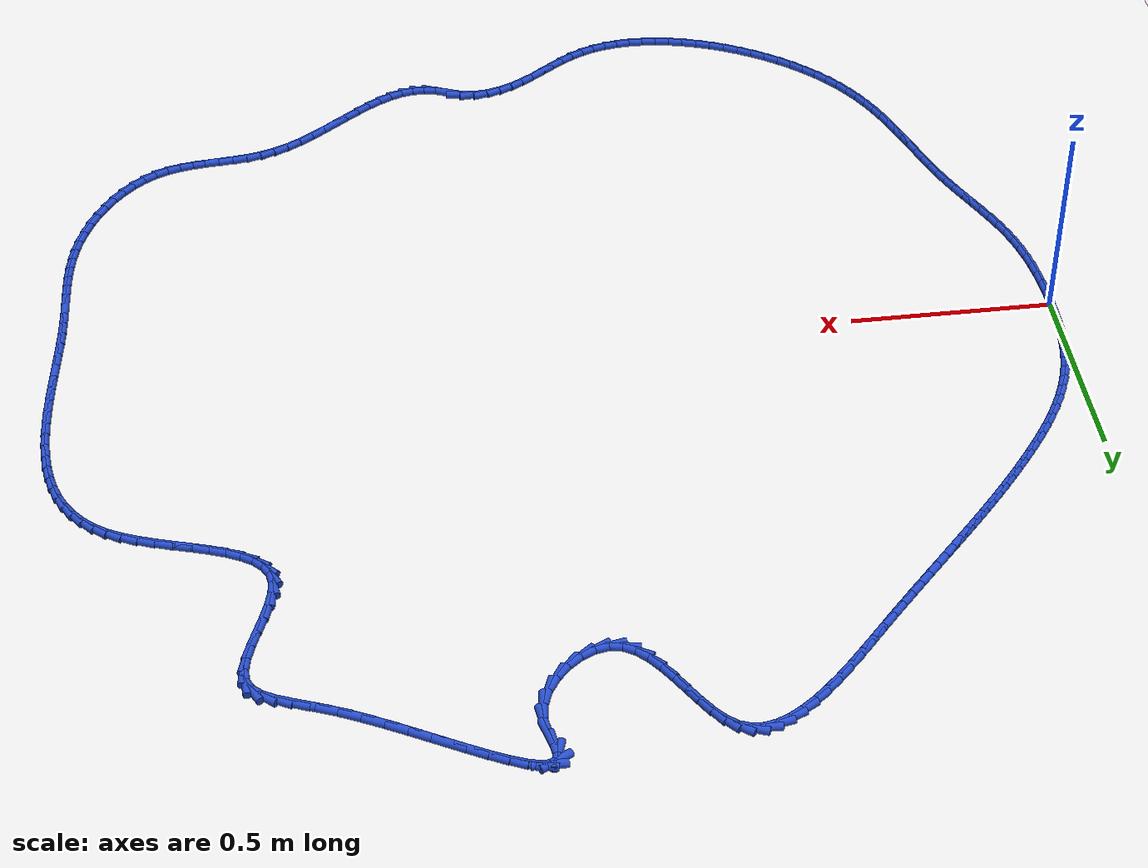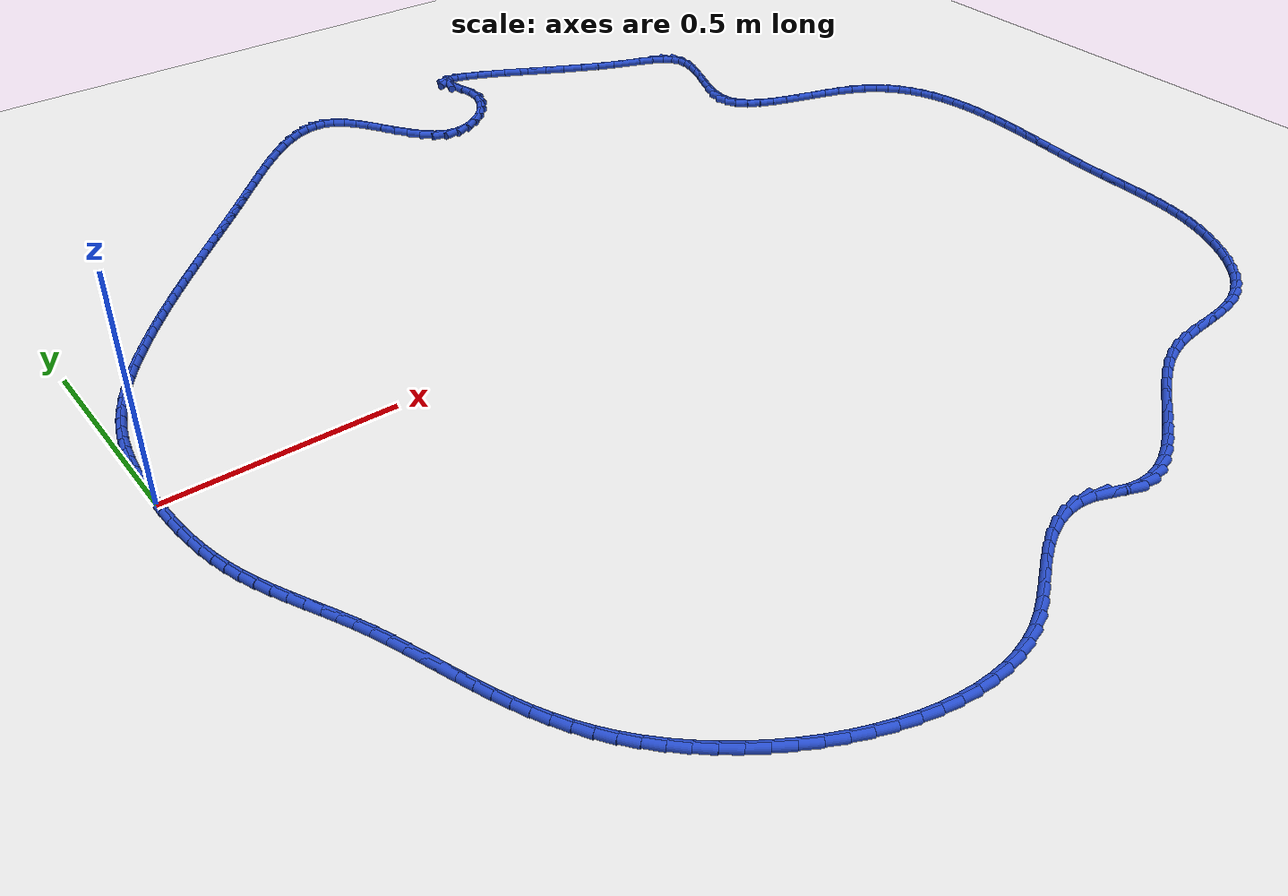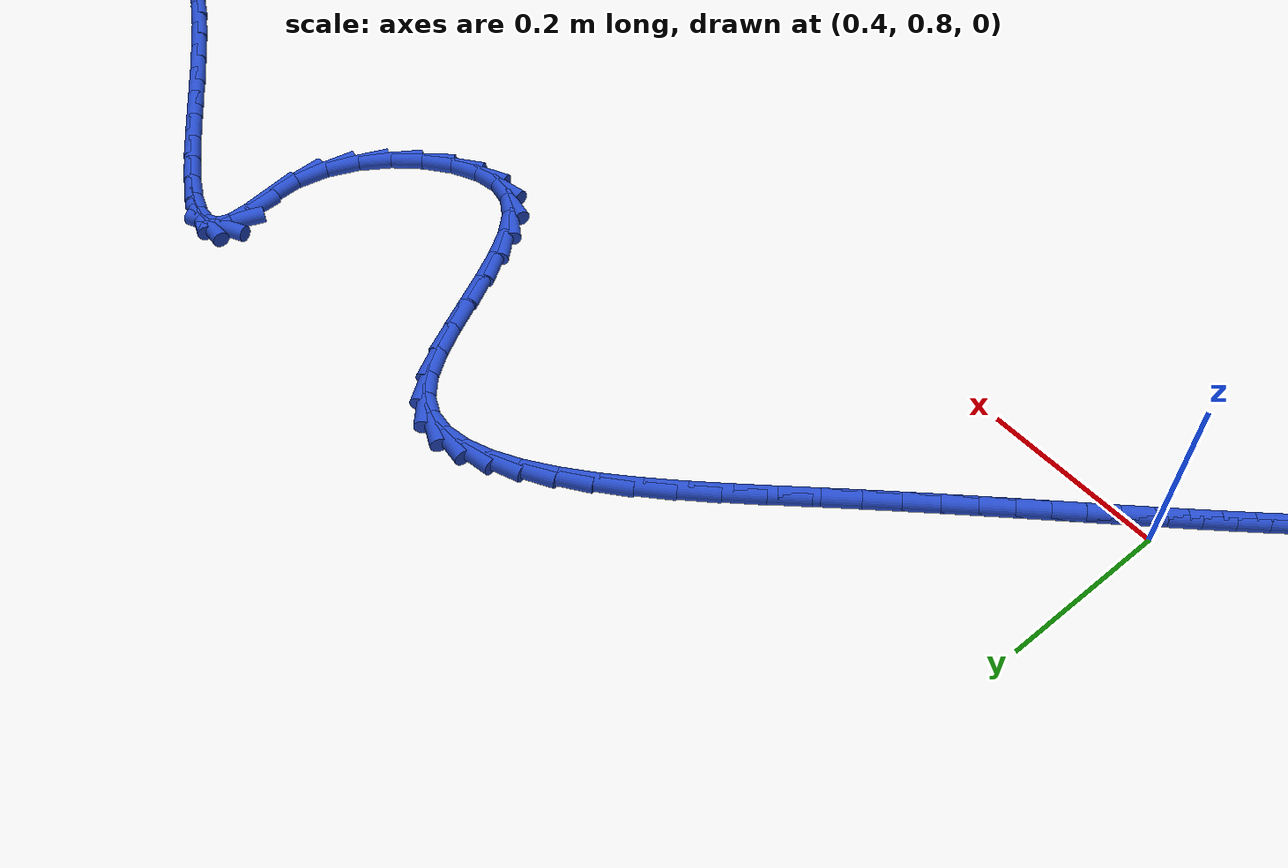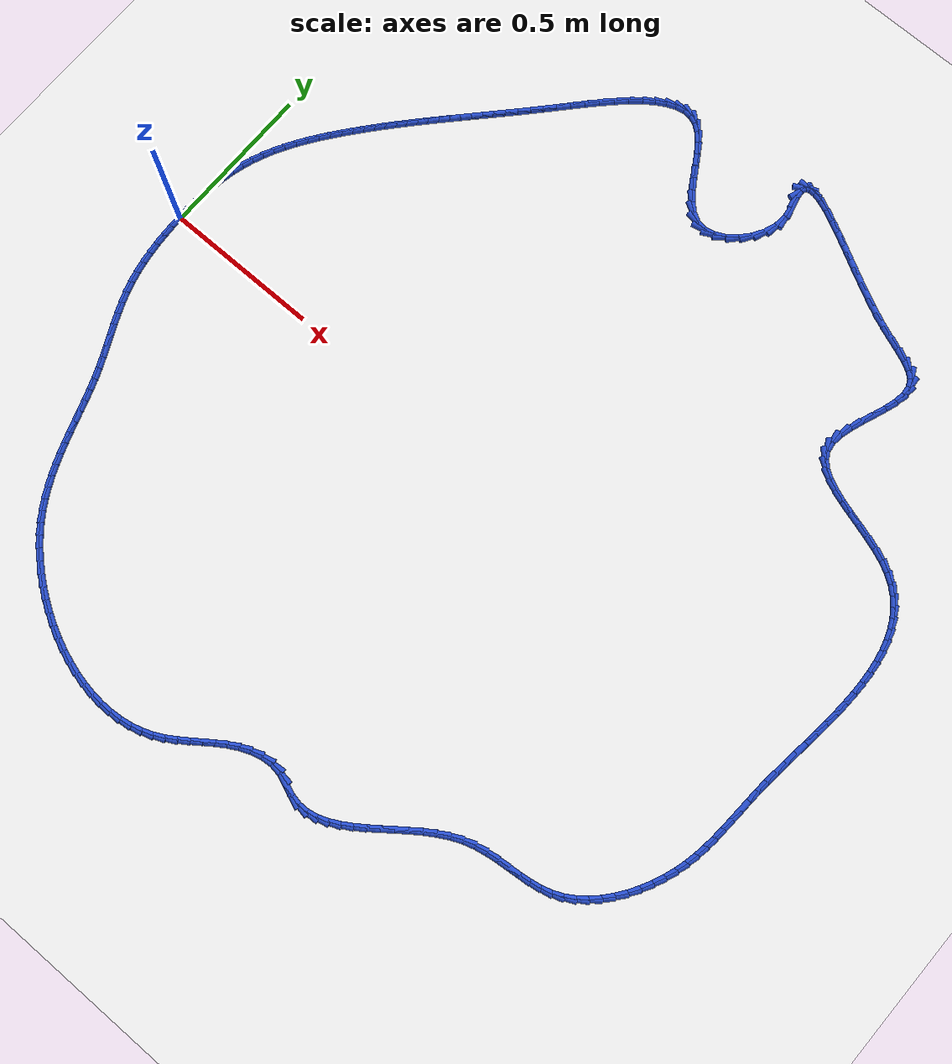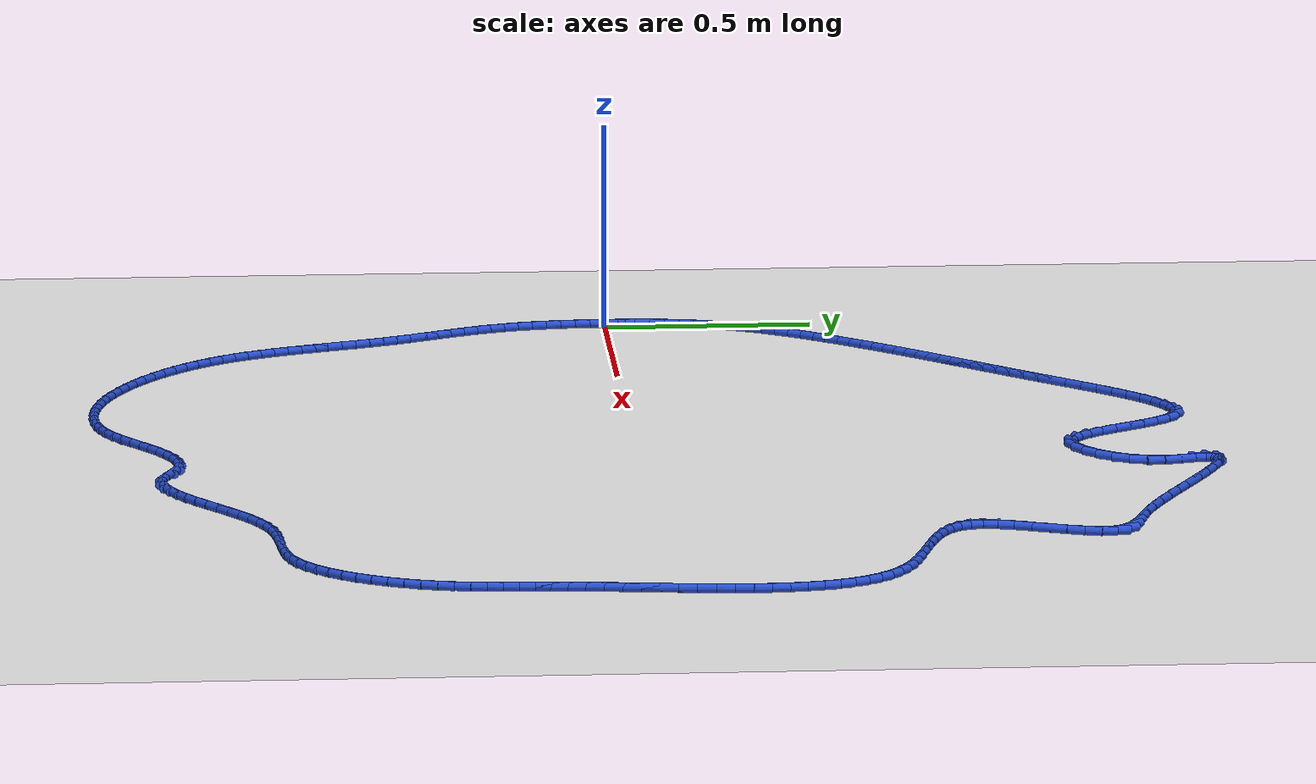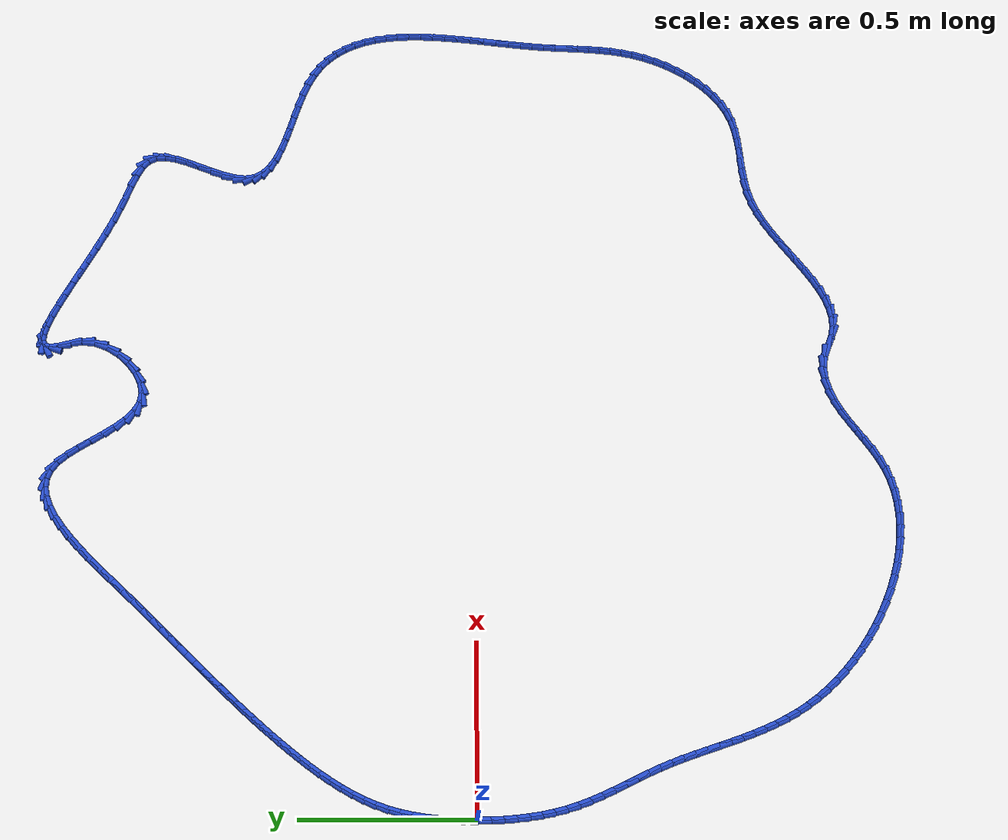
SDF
<sdf version="1.6">
 <world name="default">
  <light name="sun" type="directional">
   <pose>0 0 10 0 -0 0</pose>
   <diffuse>0.8 0.8 0.8 1</diffuse>
   <specular>0.2 0.2 0.2 1</specular>
   <attenuation>
    <range>1000</range>
    <constant>0.9</constant>
    <linear>0.01</linear>
    <quadratic>0.001</quadratic>
   </attenuation>
   <direction>-0.5 0.1 -0.9</direction>
  </light>
  <model name="ground_plane">
   <static>1</static>
   <link name="link">
    <collision name="collision">
     <geometry><plane><normal>0 0 1</normal><size>100 100</size></plane></geometry>
     <surface><friction><ode><mu>100</mu><mu2>50</mu2></ode></friction></surface>
    </collision>
    <visual name="visual">
     <cast_shadows>0</cast_shadows>
     <geometry><plane><normal>0 0 1</normal><size>100 100</size></plane></geometry>
     <material>
      <script><uri>file://media/materials/scripts/gazebo.material</uri><name>Gazebo/WhiteGlow</name></script>
     </material>
    </visual>
   </link>
  </model>
  <gravity>0 0 -9.8</gravity>
  <magnetic_field>6e-06 2.3e-05 -4.2e-05</magnetic_field>
  <atmosphere type="adiabatic"/>
  <physics name="default_physics" default="0" type="ode">
   <max_step_size>0.001</max_step_size>
   <real_time_factor>1</real_time_factor>
   <real_time_update_rate>1000</real_time_update_rate>
  </physics>
  <scene><ambient>0.4 0.4 0.4 1</ambient><background>0.7 0.7 0.7 1</background><shadows>1</shadows></scene>
  <spherical_coordinates>
   <surface_model>EARTH_WGS84</surface_model>
   <latitude_deg>0</latitude_deg>
   <longitude_deg>0</longitude_deg>
   <elevation>0</elevation>
   <heading_deg>0</heading_deg>
  </spherical_coordinates>
  <model name="line">
   <link name="link_0">
    <pose>-1.5612511283791264e-17 2.7755575615628914e-17 0.01 0 1.57 1.5645337330616884</pose>
    <collision name="collision">
     <geometry><cylinder><radius>0.01</radius><length>0.08</length></cylinder></geometry>
    </collision>
    <visual name="visual">
     <material>
      <script><name>Gazebo/Blue</name><uri>file://media/materials/scripts/gazebo.material</uri></script>
     </material>
     <geometry><cylinder><radius>0.01</radius><length>0.08</length></cylinder></geometry>
    </visual>
   </link>
   <link name="link_1">
    <pose>0.00022578573816249044 0.03605259992825206 0.01 0 1.57 1.5355703420658693</pose>
    <collision name="collision">
     <geometry><cylinder><radius>0.01</radius><length>0.08</length></cylinder></geometry>
    </collision>
    <visual name="visual">
     <material>
      <script><name>Gazebo/Blue</name><uri>file://media/materials/scripts/gazebo.material</uri></script>
     </material>
     <geometry><cylinder><radius>0.01</radius><length>0.08</length></cylinder></geometry>
    </visual>
   </link>
   <link name="link_2">
    <pose>0.0014936014654703387 0.07202863567298269 0.01 0 1.57 1.5012585992267649</pose>
    <collision name="collision">
     <geometry><cylinder><radius>0.01</radius><length>0.08</length></cylinder></geometry>
    </collision>
    <visual name="visual">
     <material>
      <script><name>Gazebo/Blue</name><uri>file://media/materials/scripts/gazebo.material</uri></script>
     </material>
     <geometry><cylinder><radius>0.01</radius><length>0.08</length></cylinder></geometry>
    </visual>
   </link>
   <link name="link_3">
    <pose>0.003988078015885075 0.10784307287168178 0.01 0 1.57 1.461422653920047</pose>
    <collision name="collision">
     <geometry><cylinder><radius>0.01</radius><length>0.08</length></cylinder></geometry>
    </collision>
    <visual name="visual">
     <material>
      <script><name>Gazebo/Blue</name><uri>file://media/materials/scripts/gazebo.material</uri></script>
     </material>
     <geometry><cylinder><radius>0.01</radius><length>0.08</length></cylinder></geometry>
    </visual>
   </link>
   <link name="link_4">
    <pose>0.007893846223368237 0.14341087716183898 0.01 0 1.57 1.4159091741670913</pose>
    <collision name="collision">
     <geometry><cylinder><radius>0.01</radius><length>0.08</length></cylinder></geometry>
    </collision>
    <visual name="visual">
     <material>
      <script><name>Gazebo/Blue</name><uri>file://media/materials/scripts/gazebo.material</uri></script>
     </material>
     <geometry><cylinder><radius>0.01</radius><length>0.08</length></cylinder></geometry>
    </visual>
   </link>
   <link name="link_5">
    <pose>0.013395536921881373 0.17864701418094417 0.01 0 1.57 1.364624998116758</pose>
    <collision name="collision">
     <geometry><cylinder><radius>0.01</radius><length>0.08</length></cylinder></geometry>
    </collision>
    <visual name="visual">
     <material>
      <script><name>Gazebo/Blue</name><uri>file://media/materials/scripts/gazebo.material</uri></script>
     </material>
     <geometry><cylinder><radius>0.01</radius><length>0.08</length></cylinder></geometry>
    </visual>
   </link>
   <link name="link_6">
    <pose>0.020677780945386033 0.21346644956648717 0.01 0 1.57 1.307582954859293</pose>
    <collision name="collision">
     <geometry><cylinder><radius>0.01</radius><length>0.08</length></cylinder></geometry>
    </collision>
    <visual name="visual">
     <material>
      <script><name>Gazebo/Blue</name><uri>file://media/materials/scripts/gazebo.material</uri></script>
     </material>
     <geometry><cylinder><radius>0.01</radius><length>0.08</length></cylinder></geometry>
    </visual>
   </link>
   <link name="link_7">
    <pose>0.02992520912784375 0.2477841489559577 0.01 0 1.57 1.2450417041647597</pose>
    <collision name="collision">
     <geometry><cylinder><radius>0.01</radius><length>0.08</length></cylinder></geometry>
    </collision>
    <visual name="visual">
     <material>
      <script><name>Gazebo/Blue</name><uri>file://media/materials/scripts/gazebo.material</uri></script>
     </material>
     <geometry><cylinder><radius>0.01</radius><length>0.08</length></cylinder></geometry>
    </visual>
   </link>
   <link name="link_8">
    <pose>0.04131927675344389 0.281515538443933 0.01 0 1.57 1.1820307072586835</pose>
    <collision name="collision">
     <geometry><cylinder><radius>0.01</radius><length>0.08</length></cylinder></geometry>
    </collision>
    <visual name="visual">
     <material>
      <script><name>Gazebo/Blue</name><uri>file://media/materials/scripts/gazebo.material</uri></script>
     </material>
     <geometry><cylinder><radius>0.01</radius><length>0.08</length></cylinder></geometry>
    </visual>
   </link>
   <link name="link_9">
    <pose>0.054871380163051854 0.31460070279872115 0.01 0 1.57 1.1255457399564834</pose>
    <collision name="collision">
     <geometry><cylinder><radius>0.01</radius><length>0.08</length></cylinder></geometry>
    </collision>
    <visual name="visual">
     <material>
      <script><name>Gazebo/Blue</name><uri>file://media/materials/scripts/gazebo.material</uri></script>
     </material>
     <geometry><cylinder><radius>0.01</radius><length>0.08</length></cylinder></geometry>
    </visual>
   </link>
   <link name="link_10">
    <pose>0.07034046776354798 0.3470163319275095 0.01 0 1.57 1.0758424300745502</pose>
    <collision name="collision">
     <geometry><cylinder><radius>0.01</radius><length>0.08</length></cylinder></geometry>
    </collision>
    <visual name="visual">
     <material>
      <script><name>Gazebo/Blue</name><uri>file://media/materials/scripts/gazebo.material</uri></script>
     </material>
     <geometry><cylinder><radius>0.01</radius><length>0.08</length></cylinder></geometry>
    </visual>
   </link>
   <link name="link_11">
    <pose>0.08746502414975428 0.37874208300551093 0.01 0 1.57 1.0325324274114127</pose>
    <collision name="collision">
     <geometry><cylinder><radius>0.01</radius><length>0.08</length></cylinder></geometry>
    </collision>
    <visual name="visual">
     <material>
      <script><name>Gazebo/Blue</name><uri>file://media/materials/scripts/gazebo.material</uri></script>
     </material>
     <geometry><cylinder><radius>0.01</radius><length>0.08</length></cylinder></geometry>
    </visual>
   </link>
   <link name="link_12">
    <pose>0.10598353391649262 0.4097576132079371 0.01 0 1.57 0.9952172512010803</pose>
    <collision name="collision">
     <geometry><cylinder><radius>0.01</radius><length>0.08</length></cylinder></geometry>
    </collision>
    <visual name="visual">
     <material>
      <script><name>Gazebo/Blue</name><uri>file://media/materials/scripts/gazebo.material</uri></script>
     </material>
     <geometry><cylinder><radius>0.01</radius><length>0.08</length></cylinder></geometry>
    </visual>
   </link>
   <link name="link_13">
    <pose>0.1256344816585849 0.4400425797100004 0.01 0 1.57 0.9635321676041322</pose>
    <collision name="collision">
     <geometry><cylinder><radius>0.01</radius><length>0.08</length></cylinder></geometry>
    </collision>
    <visual name="visual">
     <material>
      <script><name>Gazebo/Blue</name><uri>file://media/materials/scripts/gazebo.material</uri></script>
     </material>
     <geometry><cylinder><radius>0.01</radius><length>0.08</length></cylinder></geometry>
    </visual>
   </link>
   <link name="link_14">
    <pose>0.1461563519708532 0.4695766396869135 0.01 0 1.57 0.9371764914527614</pose>
    <collision name="collision">
     <geometry><cylinder><radius>0.01</radius><length>0.08</length></cylinder></geometry>
    </collision>
    <visual name="visual">
     <material>
      <script><name>Gazebo/Blue</name><uri>file://media/materials/scripts/gazebo.material</uri></script>
     </material>
     <geometry><cylinder><radius>0.01</radius><length>0.08</length></cylinder></geometry>
    </visual>
   </link>
   <link name="link_15">
    <pose>0.16728762944811928 0.4983394503138884 0.01 0 1.57 0.9159357103882878</pose>
    <collision name="collision">
     <geometry><cylinder><radius>0.01</radius><length>0.08</length></cylinder></geometry>
    </collision>
    <visual name="visual">
     <material>
      <script><name>Gazebo/Blue</name><uri>file://media/materials/scripts/gazebo.material</uri></script>
     </material>
     <geometry><cylinder><radius>0.01</radius><length>0.08</length></cylinder></geometry>
    </visual>
   </link>
   <link name="link_16">
    <pose>0.1887667986852052 0.5263106687661376 0.01 0 1.57 0.899681232305515</pose>
    <collision name="collision">
     <geometry><cylinder><radius>0.01</radius><length>0.08</length></cylinder></geometry>
    </collision>
    <visual name="visual">
     <material>
      <script><name>Gazebo/Blue</name><uri>file://media/materials/scripts/gazebo.material</uri></script>
     </material>
     <geometry><cylinder><radius>0.01</radius><length>0.08</length></cylinder></geometry>
    </visual>
   </link>
   <link name="link_17">
    <pose>0.21033366279049745 0.553470544914475 0.01 0 1.57 0.8868387783180639</pose>
    <collision name="collision">
     <geometry><cylinder><radius>0.01</radius><length>0.08</length></cylinder></geometry>
    </collision>
    <visual name="visual">
     <material>
      <script><name>Gazebo/Blue</name><uri>file://media/materials/scripts/gazebo.material</uri></script>
     </material>
     <geometry><cylinder><radius>0.01</radius><length>0.08</length></cylinder></geometry>
    </visual>
   </link>
   <link name="link_18">
    <pose>0.23183788081390969 0.5798487108546236 0.01 0 1.57 0.8747858997987897</pose>
    <collision name="collision">
     <geometry><cylinder><radius>0.01</radius><length>0.08</length></cylinder></geometry>
    </collision>
    <visual name="visual">
     <material>
      <script><name>Gazebo/Blue</name><uri>file://media/materials/scripts/gazebo.material</uri></script>
     </material>
     <geometry><cylinder><radius>0.01</radius><length>0.08</length></cylinder></geometry>
    </visual>
   </link>
   <link name="link_19">
    <pose>0.2533199095660868 0.6055605657132145 0.01 0 1.57 0.8634197215823467</pose>
    <collision name="collision">
     <geometry><cylinder><radius>0.01</radius><length>0.08</length></cylinder></geometry>
    </collision>
    <visual name="visual">
     <material>
      <script><name>Gazebo/Blue</name><uri>file://media/materials/scripts/gazebo.material</uri></script>
     </material>
     <geometry><cylinder><radius>0.01</radius><length>0.08</length></cylinder></geometry>
    </visual>
   </link>
   <link name="link_20">
    <pose>0.2748392759086999 0.6307300809483857 0.01 0 1.57 0.8529058107750099</pose>
    <collision name="collision">
     <geometry><cylinder><radius>0.01</radius><length>0.08</length></cylinder></geometry>
    </collision>
    <visual name="visual">
     <material>
      <script><name>Gazebo/Blue</name><uri>file://media/materials/scripts/gazebo.material</uri></script>
     </material>
     <geometry><cylinder><radius>0.01</radius><length>0.08</length></cylinder></geometry>
    </visual>
   </link>
   <link name="link_21">
    <pose>0.2964555067034199 0.6554812280182752 0.01 0 1.57 0.8433941527361055</pose>
    <collision name="collision">
     <geometry><cylinder><radius>0.01</radius><length>0.08</length></cylinder></geometry>
    </collision>
    <visual name="visual">
     <material>
      <script><name>Gazebo/Blue</name><uri>file://media/materials/scripts/gazebo.material</uri></script>
     </material>
     <geometry><cylinder><radius>0.01</radius><length>0.08</length></cylinder></geometry>
    </visual>
   </link>
   <link name="link_22">
    <pose>0.31822812881191803 0.6799379783810215 0.01 0 1.57 0.8350125512757378</pose>
    <collision name="collision">
     <geometry><cylinder><radius>0.01</radius><length>0.08</length></cylinder></geometry>
    </collision>
    <visual name="visual">
     <material>
      <script><name>Gazebo/Blue</name><uri>file://media/materials/scripts/gazebo.material</uri></script>
     </material>
     <geometry><cylinder><radius>0.01</radius><length>0.08</length></cylinder></geometry>
    </visual>
   </link>
   <link name="link_23">
    <pose>0.34021666909586523 0.7042243034947626 0.01 0 1.57 0.8278612711472686</pose>
    <collision name="collision">
     <geometry><cylinder><radius>0.01</radius><length>0.08</length></cylinder></geometry>
    </collision>
    <visual name="visual">
     <material>
      <script><name>Gazebo/Blue</name><uri>file://media/materials/scripts/gazebo.material</uri></script>
     </material>
     <geometry><cylinder><radius>0.01</radius><length>0.08</length></cylinder></geometry>
    </visual>
   </link>
   <link name="link_24">
    <pose>0.3624806544169326 0.7284641748176368 0.01 0 1.57 0.8220093673044713</pose>
    <collision name="collision">
     <geometry><cylinder><radius>0.01</radius><length>0.08</length></cylinder></geometry>
    </collision>
    <visual name="visual">
     <material>
      <script><name>Gazebo/Blue</name><uri>file://media/materials/scripts/gazebo.material</uri></script>
     </material>
     <geometry><cylinder><radius>0.01</radius><length>0.08</length></cylinder></geometry>
    </visual>
   </link>
   <link name="link_25">
    <pose>0.38507961163679116 0.752781563807782 0.01 0 1.57 0.817492952290413</pose>
    <collision name="collision">
     <geometry><cylinder><radius>0.01</radius><length>0.08</length></cylinder></geometry>
    </collision>
    <visual name="visual">
     <material>
      <script><name>Gazebo/Blue</name><uri>file://media/materials/scripts/gazebo.material</uri></script>
     </material>
     <geometry><cylinder><radius>0.01</radius><length>0.08</length></cylinder></geometry>
    </visual>
   </link>
   <link name="link_26">
    <pose>0.40807306761711215 0.7773004419233367 0.01 0 1.57 0.8143154357545993</pose>
    <collision name="collision">
     <geometry><cylinder><radius>0.01</radius><length>0.08</length></cylinder></geometry>
    </collision>
    <visual name="visual">
     <material>
      <script><name>Gazebo/Blue</name><uri>file://media/materials/scripts/gazebo.material</uri></script>
     </material>
     <geometry><cylinder><radius>0.01</radius><length>0.08</length></cylinder></geometry>
    </visual>
   </link>
   <link name="link_27">
    <pose>0.4315205492195664 0.8021447806224388 0.01 0 1.57 0.8124495658760261</pose>
    <collision name="collision">
     <geometry><cylinder><radius>0.01</radius><length>0.08</length></cylinder></geometry>
    </collision>
    <visual name="visual">
     <material>
      <script><name>Gazebo/Blue</name><uri>file://media/materials/scripts/gazebo.material</uri></script>
     </material>
     <geometry><cylinder><radius>0.01</radius><length>0.08</length></cylinder></geometry>
    </visual>
   </link>
   <link name="link_28">
    <pose>0.4554815833058252 0.8274385513632267 0.01 0 1.57 0.8118409420401287</pose>
    <collision name="collision">
     <geometry><cylinder><radius>0.01</radius><length>0.08</length></cylinder></geometry>
    </collision>
    <visual name="visual">
     <material>
      <script><name>Gazebo/Blue</name><uri>file://media/materials/scripts/gazebo.material</uri></script>
     </material>
     <geometry><cylinder><radius>0.01</radius><length>0.08</length></cylinder></geometry>
    </visual>
   </link>
   <link name="link_29">
    <pose>0.48001569673755934 0.8533057256038382 0.01 0 1.57 0.8124125695661213</pose>
    <collision name="collision">
     <geometry><cylinder><radius>0.01</radius><length>0.08</length></cylinder></geometry>
    </collision>
    <visual name="visual">
     <material>
      <script><name>Gazebo/Blue</name><uri>file://media/materials/scripts/gazebo.material</uri></script>
     </material>
     <geometry><cylinder><radius>0.01</radius><length>0.08</length></cylinder></geometry>
    </visual>
   </link>
   <link name="link_30">
    <pose>0.5051824163764401 0.8798702748024116 0.01 0 1.57 0.8140699946064636</pose>
    <collision name="collision">
     <geometry><cylinder><radius>0.01</radius><length>0.08</length></cylinder></geometry>
    </collision>
    <visual name="visual">
     <material>
      <script><name>Gazebo/Blue</name><uri>file://media/materials/scripts/gazebo.material</uri></script>
     </material>
     <geometry><cylinder><radius>0.01</radius><length>0.08</length></cylinder></geometry>
    </visual>
   </link>
   <link name="link_31">
    <pose>0.5310412690841384 0.9072561704170854 0.01 0 1.57 0.8167065826098714</pose>
    <collision name="collision">
     <geometry><cylinder><radius>0.01</radius><length>0.08</length></cylinder></geometry>
    </collision>
    <visual name="visual">
     <material>
      <script><name>Gazebo/Blue</name><uri>file://media/materials/scripts/gazebo.material</uri></script>
     </material>
     <geometry><cylinder><radius>0.01</radius><length>0.08</length></cylinder></geometry>
    </visual>
   </link>
   <link name="link_32">
    <pose>0.5576517817223257 0.9355873839059977 0.01 0 1.57 0.8202085714201305</pose>
    <collision name="collision">
     <geometry><cylinder><radius>0.01</radius><length>0.08</length></cylinder></geometry>
    </collision>
    <visual name="visual">
     <material>
      <script><name>Gazebo/Blue</name><uri>file://media/materials/scripts/gazebo.material</uri></script>
     </material>
     <geometry><cylinder><radius>0.01</radius><length>0.08</length></cylinder></geometry>
    </visual>
   </link>
   <link name="link_33">
    <pose>0.5850734811526723 0.9649878867272863 0.01 0 1.57 0.8244596218350776</pose>
    <collision name="collision">
     <geometry><cylinder><radius>0.01</radius><length>0.08</length></cylinder></geometry>
    </collision>
    <visual name="visual">
     <material>
      <script><name>Gazebo/Blue</name><uri>file://media/materials/scripts/gazebo.material</uri></script>
     </material>
     <geometry><cylinder><radius>0.01</radius><length>0.08</length></cylinder></geometry>
    </visual>
   </link>
   <link name="link_34">
    <pose>0.61336589423685 0.9955816503390893 0.01 0 1.57 0.8293444780642792</pose>
    <collision name="collision">
     <geometry><cylinder><radius>0.01</radius><length>0.08</length></cylinder></geometry>
    </collision>
    <visual name="visual">
     <material>
      <script><name>Gazebo/Blue</name><uri>file://media/materials/scripts/gazebo.material</uri></script>
     </material>
     <geometry><cylinder><radius>0.01</radius><length>0.08</length></cylinder></geometry>
    </visual>
   </link>
   <link name="link_35">
    <pose>0.6425885422428071 1.027492626697952 0.01 0 1.57 0.8327669592573147</pose>
    <collision name="collision">
     <geometry><cylinder><radius>0.01</radius><length>0.08</length></cylinder></geometry>
    </collision>
    <visual name="visual">
     <material>
      <script><name>Gazebo/Blue</name><uri>file://media/materials/scripts/gazebo.material</uri></script>
     </material>
     <geometry><cylinder><radius>0.01</radius><length>0.08</length></cylinder></geometry>
    </visual>
   </link>
   <link name="link_36">
    <pose>0.672745306359458 1.060650787763983 0.01 0 1.57 0.8281542361408051</pose>
    <collision name="collision">
     <geometry><cylinder><radius>0.01</radius><length>0.08</length></cylinder></geometry>
    </collision>
    <visual name="visual">
     <material>
      <script><name>Gazebo/Blue</name><uri>file://media/materials/scripts/gazebo.material</uri></script>
     </material>
     <geometry><cylinder><radius>0.01</radius><length>0.08</length></cylinder></geometry>
    </visual>
   </link>
   <link name="link_37">
    <pose>0.7036477224962082 1.0943155252738246 0.01 0 1.57 0.8142575172836231</pose>
    <collision name="collision">
     <geometry><cylinder><radius>0.01</radius><length>0.08</length></cylinder></geometry>
    </collision>
    <visual name="visual">
     <material>
      <script><name>Gazebo/Blue</name><uri>file://media/materials/scripts/gazebo.material</uri></script>
     </material>
     <geometry><cylinder><radius>0.01</radius><length>0.08</length></cylinder></geometry>
    </visual>
   </link>
   <link name="link_38">
    <pose>0.7350657922717315 1.1276014284816642 0.01 0 1.57 0.7903872348356703</pose>
    <collision name="collision">
     <geometry><cylinder><radius>0.01</radius><length>0.08</length></cylinder></geometry>
    </collision>
    <visual name="visual">
     <material>
      <script><name>Gazebo/Blue</name><uri>file://media/materials/scripts/gazebo.material</uri></script>
     </material>
     <geometry><cylinder><radius>0.01</radius><length>0.08</length></cylinder></geometry>
    </visual>
   </link>
   <link name="link_39">
    <pose>0.7667695173047027 1.1596230866416912 0.01 0 1.57 0.7547840550857329</pose>
    <collision name="collision">
     <geometry><cylinder><radius>0.01</radius><length>0.08</length></cylinder></geometry>
    </collision>
    <visual name="visual">
     <material>
      <script><name>Gazebo/Blue</name><uri>file://media/materials/scripts/gazebo.material</uri></script>
     </material>
     <geometry><cylinder><radius>0.01</radius><length>0.08</length></cylinder></geometry>
    </visual>
   </link>
   <link name="link_40">
    <pose>0.7985288992137948 1.189495089008094 0.01 0 1.57 0.7043038217005845</pose>
    <collision name="collision">
     <geometry><cylinder><radius>0.01</radius><length>0.08</length></cylinder></geometry>
    </collision>
    <visual name="visual">
     <material>
      <script><name>Gazebo/Blue</name><uri>file://media/materials/scripts/gazebo.material</uri></script>
     </material>
     <geometry><cylinder><radius>0.01</radius><length>0.08</length></cylinder></geometry>
    </visual>
   </link>
   <link name="link_41">
    <pose>0.8301139396176819 1.21633202483506 0.01 0 1.57 0.6338035461217338</pose>
    <collision name="collision">
     <geometry><cylinder><radius>0.01</radius><length>0.08</length></cylinder></geometry>
    </collision>
    <visual name="visual">
     <material>
      <script><name>Gazebo/Blue</name><uri>file://media/materials/scripts/gazebo.material</uri></script>
     </material>
     <geometry><cylinder><radius>0.01</radius><length>0.08</length></cylinder></geometry>
    </visual>
   </link>
   <link name="link_42">
    <pose>0.8612946401350379 1.2392484833767785 0.01 0 1.57 0.5351736500281211</pose>
    <collision name="collision">
     <geometry><cylinder><radius>0.01</radius><length>0.08</length></cylinder></geometry>
    </collision>
    <visual name="visual">
     <material>
      <script><name>Gazebo/Blue</name><uri>file://media/materials/scripts/gazebo.material</uri></script>
     </material>
     <geometry><cylinder><radius>0.01</radius><length>0.08</length></cylinder></geometry>
    </visual>
   </link>
   <link name="link_43">
    <pose>0.8918410023845367 1.2573590538874373 0.01 0 1.57 0.3962760851739158</pose>
    <collision name="collision">
     <geometry><cylinder><radius>0.01</radius><length>0.08</length></cylinder></geometry>
    </collision>
    <visual name="visual">
     <material>
      <script><name>Gazebo/Blue</name><uri>file://media/materials/scripts/gazebo.material</uri></script>
     </material>
     <geometry><cylinder><radius>0.01</radius><length>0.08</length></cylinder></geometry>
    </visual>
   </link>
   <link name="link_44">
    <pose>0.9215230279848526 1.269778325621226 0.01 0 1.57 0.20159714972996667</pose>
    <collision name="collision">
     <geometry><cylinder><radius>0.01</radius><length>0.08</length></cylinder></geometry>
    </collision>
    <visual name="visual">
     <material>
      <script><name>Gazebo/Blue</name><uri>file://media/materials/scripts/gazebo.material</uri></script>
     </material>
     <geometry><cylinder><radius>0.01</radius><length>0.08</length></cylinder></geometry>
    </visual>
   </link>
   <link name="link_45">
    <pose>0.9501107185546588 1.2756208878323316 0.01 0 1.57 -0.059334476204864005</pose>
    <collision name="collision">
     <geometry><cylinder><radius>0.01</radius><length>0.08</length></cylinder></geometry>
    </collision>
    <visual name="visual">
     <material>
      <script><name>Gazebo/Blue</name><uri>file://media/materials/scripts/gazebo.material</uri></script>
     </material>
     <geometry><cylinder><radius>0.01</radius><length>0.08</length></cylinder></geometry>
    </visual>
   </link>
   <link name="link_46">
    <pose>0.9773740757126297 1.2740013297749435 0.01 0 1.57 -0.3698480200925227</pose>
    <collision name="collision">
     <geometry><cylinder><radius>0.01</radius><length>0.08</length></cylinder></geometry>
    </collision>
    <visual name="visual">
     <material>
      <script><name>Gazebo/Blue</name><uri>file://media/materials/scripts/gazebo.material</uri></script>
     </material>
     <geometry><cylinder><radius>0.01</radius><length>0.08</length></cylinder></geometry>
    </visual>
   </link>
   <link name="link_47">
    <pose>1.0030831010774388 1.2640342407032494 0.01 0 1.57 -0.6677014612844325</pose>
    <collision name="collision">
     <geometry><cylinder><radius>0.01</radius><length>0.08</length></cylinder></geometry>
    </collision>
    <visual name="visual">
     <material>
      <script><name>Gazebo/Blue</name><uri>file://media/materials/scripts/gazebo.material</uri></script>
     </material>
     <geometry><cylinder><radius>0.01</radius><length>0.08</length></cylinder></geometry>
    </visual>
   </link>
   <link name="link_48">
    <pose>1.0270747734851597 1.24511633404198 0.01 0 1.57 -0.8643878954026266</pose>
    <collision name="collision">
     <geometry><cylinder><radius>0.01</radius><length>0.08</length></cylinder></geometry>
    </collision>
    <visual name="visual">
     <material>
      <script><name>Gazebo/Blue</name><uri>file://media/materials/scripts/gazebo.material</uri></script>
     </material>
     <geometry><cylinder><radius>0.01</radius><length>0.08</length></cylinder></geometry>
    </visual>
   </link>
   <link name="link_49">
    <pose>1.0496614308575394 1.2186466501706428 0.01 0 1.57 -0.9713565475624298</pose>
    <collision name="collision">
     <geometry><cylinder><radius>0.01</radius><length>0.08</length></cylinder></geometry>
    </collision>
    <visual name="visual">
     <material>
      <script><name>Gazebo/Blue</name><uri>file://media/materials/scripts/gazebo.material</uri></script>
     </material>
     <geometry><cylinder><radius>0.01</radius><length>0.08</length></cylinder></geometry>
    </visual>
   </link>
   <link name="link_50">
    <pose>1.071361017196465 1.186890291796655 0.01 0 1.57 -1.020569207023786</pose>
    <collision name="collision">
     <geometry><cylinder><radius>0.01</radius><length>0.08</length></cylinder></geometry>
    </collision>
    <visual name="visual">
     <material>
      <script><name>Gazebo/Blue</name><uri>file://media/materials/scripts/gazebo.material</uri></script>
     </material>
     <geometry><cylinder><radius>0.01</radius><length>0.08</length></cylinder></geometry>
    </visual>
   </link>
   <link name="link_51">
    <pose>1.0926922969543313 1.1521158175625679 0.01 0 1.57 -1.0269207747158406</pose>
    <collision name="collision">
     <geometry><cylinder><radius>0.01</radius><length>0.08</length></cylinder></geometry>
    </collision>
    <visual name="visual">
     <material>
      <script><name>Gazebo/Blue</name><uri>file://media/materials/scripts/gazebo.material</uri></script>
     </material>
     <geometry><cylinder><radius>0.01</radius><length>0.08</length></cylinder></geometry>
    </visual>
   </link>
   <link name="link_52">
    <pose>1.1141740345835331 1.116591786110933 0.01 0 1.57 -0.9934358311492614</pose>
    <collision name="collision">
     <geometry><cylinder><radius>0.01</radius><length>0.08</length></cylinder></geometry>
    </collision>
    <visual name="visual">
     <material>
      <script><name>Gazebo/Blue</name><uri>file://media/materials/scripts/gazebo.material</uri></script>
     </material>
     <geometry><cylinder><radius>0.01</radius><length>0.08</length></cylinder></geometry>
    </visual>
   </link>
   <link name="link_53">
    <pose>1.1363249945364646 1.0825867560843017 0.01 0 1.57 -0.9131339587827015</pose>
    <collision name="collision">
     <geometry><cylinder><radius>0.01</radius><length>0.08</length></cylinder></geometry>
    </collision>
    <visual name="visual">
     <material>
      <script><name>Gazebo/Blue</name><uri>file://media/materials/scripts/gazebo.material</uri></script>
     </material>
     <geometry><cylinder><radius>0.01</radius><length>0.08</length></cylinder></geometry>
    </visual>
   </link>
   <link name="link_54">
    <pose>1.1596639412655207 1.052369286125226 0.01 0 1.57 -0.7674281463106903</pose>
    <collision name="collision">
     <geometry><cylinder><radius>0.01</radius><length>0.08</length></cylinder></geometry>
    </collision>
    <visual name="visual">
     <material>
      <script><name>Gazebo/Blue</name><uri>file://media/materials/scripts/gazebo.material</uri></script>
     </material>
     <geometry><cylinder><radius>0.01</radius><length>0.08</length></cylinder></geometry>
    </visual>
   </link>
   <link name="link_55">
    <pose>1.1847096392230956 1.0282079348762572 0.01 0 1.57 -0.5261151114894413</pose>
    <collision name="collision">
     <geometry><cylinder><radius>0.01</radius><length>0.08</length></cylinder></geometry>
    </collision>
    <visual name="visual">
     <material>
      <script><name>Gazebo/Blue</name><uri>file://media/materials/scripts/gazebo.material</uri></script>
     </material>
     <geometry><cylinder><radius>0.01</radius><length>0.08</length></cylinder></geometry>
    </visual>
   </link>
   <link name="link_56">
    <pose>1.211980852861584 1.012371260979947 0.01 0 1.57 -0.17339602639009377</pose>
    <collision name="collision">
     <geometry><cylinder><radius>0.01</radius><length>0.08</length></cylinder></geometry>
    </collision>
    <visual name="visual">
     <material>
      <script><name>Gazebo/Blue</name><uri>file://media/materials/scripts/gazebo.material</uri></script>
     </material>
     <geometry><cylinder><radius>0.01</radius><length>0.08</length></cylinder></geometry>
    </visual>
   </link>
   <link name="link_57">
    <pose>1.2419883490674897 1.007115298918545 0.01 0 1.57 0.19095225686706108</pose>
    <collision name="collision">
     <geometry><cylinder><radius>0.01</radius><length>0.08</length></cylinder></geometry>
    </collision>
    <visual name="visual">
     <material>
      <script><name>Gazebo/Blue</name><uri>file://media/materials/scripts/gazebo.material</uri></script>
     </material>
     <geometry><cylinder><radius>0.01</radius><length>0.08</length></cylinder></geometry>
    </visual>
   </link>
   <link name="link_58">
    <pose>1.27440335185343 1.0133813619609107 0.01 0 1.57 0.4591046806819367</pose>
    <collision name="collision">
     <geometry><cylinder><radius>0.01</radius><length>0.08</length></cylinder></geometry>
    </collision>
    <visual name="visual">
     <material>
      <script><name>Gazebo/Blue</name><uri>file://media/materials/scripts/gazebo.material</uri></script>
     </material>
     <geometry><cylinder><radius>0.01</radius><length>0.08</length></cylinder></geometry>
    </visual>
   </link>
   <link name="link_59">
    <pose>1.3073313212078126 1.029658782373113 0.01 0 1.57 0.6631665294617721</pose>
    <collision name="collision">
     <geometry><cylinder><radius>0.01</radius><length>0.08</length></cylinder></geometry>
    </collision>
    <visual name="visual">
     <material>
      <script><name>Gazebo/Blue</name><uri>file://media/materials/scripts/gazebo.material</uri></script>
     </material>
     <geometry><cylinder><radius>0.01</radius><length>0.08</length></cylinder></geometry>
    </visual>
   </link>
   <link name="link_60">
    <pose>1.3387065401874547 1.0541688299431722 0.01 0 1.57 0.8399617097013284</pose>
    <collision name="collision">
     <geometry><cylinder><radius>0.01</radius><length>0.08</length></cylinder></geometry>
    </collision>
    <visual name="visual">
     <material>
      <script><name>Gazebo/Blue</name><uri>file://media/materials/scripts/gazebo.material</uri></script>
     </material>
     <geometry><cylinder><radius>0.01</radius><length>0.08</length></cylinder></geometry>
    </visual>
   </link>
   <link name="link_61">
    <pose>1.3664632918491753 1.085132774459108 0.01 0 1.57 1.0162807211615397</pose>
    <collision name="collision">
     <geometry><cylinder><radius>0.01</radius><length>0.08</length></cylinder></geometry>
    </collision>
    <visual name="visual">
     <material>
      <script><name>Gazebo/Blue</name><uri>file://media/materials/scripts/gazebo.material</uri></script>
     </material>
     <geometry><cylinder><radius>0.01</radius><length>0.08</length></cylinder></geometry>
    </visual>
   </link>
   <link name="link_62">
    <pose>1.388535859249792 1.1207718857089404 0.01 0 1.57 1.2149446711378429</pose>
    <collision name="collision">
     <geometry><cylinder><radius>0.01</radius><length>0.08</length></cylinder></geometry>
    </collision>
    <visual name="visual">
     <material>
      <script><name>Gazebo/Blue</name><uri>file://media/materials/scripts/gazebo.material</uri></script>
     </material>
     <geometry><cylinder><radius>0.01</radius><length>0.08</length></cylinder></geometry>
    </visual>
   </link>
   <link name="link_63">
    <pose>1.4028585254461239 1.1593074334806899 0.01 0 1.57 1.4576205246210694</pose>
    <collision name="collision">
     <geometry><cylinder><radius>0.01</radius><length>0.08</length></cylinder></geometry>
    </collision>
    <visual name="visual">
     <material>
      <script><name>Gazebo/Blue</name><uri>file://media/materials/scripts/gazebo.material</uri></script>
     </material>
     <geometry><cylinder><radius>0.01</radius><length>0.08</length></cylinder></geometry>
    </visual>
   </link>
   <link name="link_64">
    <pose>1.4073655739645103 1.1989606874662364 0.01 0 1.57 -1.4282237736679075</pose>
    <collision name="collision">
     <geometry><cylinder><radius>0.01</radius><length>0.08</length></cylinder></geometry>
    </collision>
    <visual name="visual">
     <material>
      <script><name>Gazebo/Blue</name><uri>file://media/materials/scripts/gazebo.material</uri></script>
     </material>
     <geometry><cylinder><radius>0.01</radius><length>0.08</length></cylinder></geometry>
    </visual>
   </link>
   <link name="link_65">
    <pose>1.4018221910491404 1.2375780216332153 0.01 0 1.57 -1.3215268080966618</pose>
    <collision name="collision">
     <geometry><cylinder><radius>0.01</radius><length>0.08</length></cylinder></geometry>
    </collision>
    <visual name="visual">
     <material>
      <script><name>Gazebo/Blue</name><uri>file://media/materials/scripts/gazebo.material</uri></script>
     </material>
     <geometry><cylinder><radius>0.01</radius><length>0.08</length></cylinder></geometry>
    </visual>
   </link>
   <link name="link_66">
    <pose>1.3931780405376624 1.271534715988635 0.01 0 1.57 -1.4402197359903461</pose>
    <collision name="collision">
     <geometry><cylinder><radius>0.01</radius><length>0.08</length></cylinder></geometry>
    </collision>
    <visual name="visual">
     <material>
      <script><name>Gazebo/Blue</name><uri>file://media/materials/scripts/gazebo.material</uri></script>
     </material>
     <geometry><cylinder><radius>0.01</radius><length>0.08</length></cylinder></geometry>
    </visual>
   </link>
   <link name="link_67">
    <pose>1.3898326392571394 1.297009162118401 0.01 0 1.57 1.2465438670802291</pose>
    <collision name="collision">
     <geometry><cylinder><radius>0.01</radius><length>0.08</length></cylinder></geometry>
    </collision>
    <visual name="visual">
     <material>
      <script><name>Gazebo/Blue</name><uri>file://media/materials/scripts/gazebo.material</uri></script>
     </material>
     <geometry><cylinder><radius>0.01</radius><length>0.08</length></cylinder></geometry>
    </visual>
   </link>
   <link name="link_68">
    <pose>1.3951484483361516 1.3128245833693972 0.01 0 1.57 0.4925253742733426</pose>
    <collision name="collision">
     <geometry><cylinder><radius>0.01</radius><length>0.08</length></cylinder></geometry>
    </collision>
    <visual name="visual">
     <material>
      <script><name>Gazebo/Blue</name><uri>file://media/materials/scripts/gazebo.material</uri></script>
     </material>
     <geometry><cylinder><radius>0.01</radius><length>0.08</length></cylinder></geometry>
    </visual>
   </link>
   <link name="link_69">
    <pose>1.4084139624288243 1.3199433408248649 0.01 0 1.57 -0.027178209342349713</pose>
    <collision name="collision">
     <geometry><cylinder><radius>0.01</radius><length>0.08</length></cylinder></geometry>
    </collision>
    <visual name="visual">
     <material>
      <script><name>Gazebo/Blue</name><uri>file://media/materials/scripts/gazebo.material</uri></script>
     </material>
     <geometry><cylinder><radius>0.01</radius><length>0.08</length></cylinder></geometry>
    </visual>
   </link>
   <link name="link_70">
    <pose>1.4288008757315973 1.3193891245623415 0.01 0 1.57 -0.263708274332721</pose>
    <collision name="collision">
     <geometry><cylinder><radius>0.01</radius><length>0.08</length></cylinder></geometry>
    </collision>
    <visual name="visual">
     <material>
      <script><name>Gazebo/Blue</name><uri>file://media/materials/scripts/gazebo.material</uri></script>
     </material>
     <geometry><cylinder><radius>0.01</radius><length>0.08</length></cylinder></geometry>
    </visual>
   </link>
   <link name="link_71">
    <pose>1.4554808824409091 1.3121856246593635 0.01 0 1.57 -0.3797331203396081</pose>
    <collision name="collision">
     <geometry><cylinder><radius>0.01</radius><length>0.08</length></cylinder></geometry>
    </collision>
    <visual name="visual">
     <material>
      <script><name>Gazebo/Blue</name><uri>file://media/materials/scripts/gazebo.material</uri></script>
     </material>
     <geometry><cylinder><radius>0.01</radius><length>0.08</length></cylinder></geometry>
    </visual>
   </link>
   <link name="link_72">
    <pose>1.4876256767531997 1.2993565311934674 0.01 0 1.57 -0.44255822764517266</pose>
    <collision name="collision">
     <geometry><cylinder><radius>0.01</radius><length>0.08</length></cylinder></geometry>
    </collision>
    <visual name="visual">
     <material>
      <script><name>Gazebo/Blue</name><uri>file://media/materials/scripts/gazebo.material</uri></script>
     </material>
     <geometry><cylinder><radius>0.01</radius><length>0.08</length></cylinder></geometry>
    </visual>
   </link>
   <link name="link_73">
    <pose>1.5244069528649078 1.28192553424219 0.01 0 1.57 -0.47763040421585945</pose>
    <collision name="collision">
     <geometry><cylinder><radius>0.01</radius><length>0.08</length></cylinder></geometry>
    </collision>
    <visual name="visual">
     <material>
      <script><name>Gazebo/Blue</name><uri>file://media/materials/scripts/gazebo.material</uri></script>
     </material>
     <geometry><cylinder><radius>0.01</radius><length>0.08</length></cylinder></geometry>
    </visual>
   </link>
   <link name="link_74">
    <pose>1.5649964049724727 1.2609163238830672 0.01 0 1.57 -0.4957780890466638</pose>
    <collision name="collision">
     <geometry><cylinder><radius>0.01</radius><length>0.08</length></cylinder></geometry>
    </collision>
    <visual name="visual">
     <material>
      <script><name>Gazebo/Blue</name><uri>file://media/materials/scripts/gazebo.material</uri></script>
     </material>
     <geometry><cylinder><radius>0.01</radius><length>0.08</length></cylinder></geometry>
    </visual>
   </link>
   <link name="link_75">
    <pose>1.6085657272723333 1.2373525901936357 0.01 0 1.57 -0.501970929425132</pose>
    <collision name="collision">
     <geometry><cylinder><radius>0.01</radius><length>0.08</length></cylinder></geometry>
    </collision>
    <visual name="visual">
     <material>
      <script><name>Gazebo/Blue</name><uri>file://media/materials/scripts/gazebo.material</uri></script>
     </material>
     <geometry><cylinder><radius>0.01</radius><length>0.08</length></cylinder></geometry>
    </visual>
   </link>
   <link name="link_76">
    <pose>1.654286613960929 1.2122580232514328 0.01 0 1.57 -0.4983840273901671</pose>
    <collision name="collision">
     <geometry><cylinder><radius>0.01</radius><length>0.08</length></cylinder></geometry>
    </collision>
    <visual name="visual">
     <material>
      <script><name>Gazebo/Blue</name><uri>file://media/materials/scripts/gazebo.material</uri></script>
     </material>
     <geometry><cylinder><radius>0.01</radius><length>0.08</length></cylinder></geometry>
    </visual>
   </link>
   <link name="link_77">
    <pose>1.7013307592346991 1.1866563131339936 0.01 0 1.57 -0.4855412042509985</pose>
    <collision name="collision">
     <geometry><cylinder><radius>0.01</radius><length>0.08</length></cylinder></geometry>
    </collision>
    <visual name="visual">
     <material>
      <script><name>Gazebo/Blue</name><uri>file://media/materials/scripts/gazebo.material</uri></script>
     </material>
     <geometry><cylinder><radius>0.01</radius><length>0.08</length></cylinder></geometry>
    </visual>
   </link>
   <link name="link_78">
    <pose>1.7488698572900825 1.1615711499188561 0.01 0 1.57 -0.4626651060630524</pose>
    <collision name="collision">
     <geometry><cylinder><radius>0.01</radius><length>0.08</length></cylinder></geometry>
    </collision>
    <visual name="visual">
     <material>
      <script><name>Gazebo/Blue</name><uri>file://media/materials/scripts/gazebo.material</uri></script>
     </material>
     <geometry><cylinder><radius>0.01</radius><length>0.08</length></cylinder></geometry>
    </visual>
   </link>
   <link name="link_79">
    <pose>1.7960756023235185 1.1380262236835554 0.01 0 1.57 -0.4275607105560348</pose>
    <collision name="collision">
     <geometry><cylinder><radius>0.01</radius><length>0.08</length></cylinder></geometry>
    </collision>
    <visual name="visual">
     <material>
      <script><name>Gazebo/Blue</name><uri>file://media/materials/scripts/gazebo.material</uri></script>
     </material>
     <geometry><cylinder><radius>0.01</radius><length>0.08</length></cylinder></geometry>
    </visual>
   </link>
   <link name="link_80">
    <pose>1.842119688531446 1.1170452245056293 0.01 0 1.57 -0.3815676326231116</pose>
    <collision name="collision">
     <geometry><cylinder><radius>0.01</radius><length>0.08</length></cylinder></geometry>
    </collision>
    <visual name="visual">
     <material>
      <script><name>Gazebo/Blue</name><uri>file://media/materials/scripts/gazebo.material</uri></script>
     </material>
     <geometry><cylinder><radius>0.01</radius><length>0.08</length></cylinder></geometry>
    </visual>
   </link>
   <link name="link_81">
    <pose>1.8861082369021789 1.099395629755753 0.01 0 1.57 -0.36101320353402433</pose>
    <collision name="collision">
     <geometry><cylinder><radius>0.01</radius><length>0.08</length></cylinder></geometry>
    </collision>
    <visual name="visual">
     <material>
      <script><name>Gazebo/Blue</name><uri>file://media/materials/scripts/gazebo.material</uri></script>
     </material>
     <geometry><cylinder><radius>0.01</radius><length>0.08</length></cylinder></geometry>
    </visual>
   </link>
   <link name="link_82">
    <pose>1.9266936701131725 1.08407219169864 0.01 0 1.57 -0.39242027149229514</pose>
    <collision name="collision">
     <geometry><cylinder><radius>0.01</radius><length>0.08</length></cylinder></geometry>
    </collision>
    <visual name="visual">
     <material>
      <script><name>Gazebo/Blue</name><uri>file://media/materials/scripts/gazebo.material</uri></script>
     </material>
     <geometry><cylinder><radius>0.01</radius><length>0.08</length></cylinder></geometry>
    </visual>
   </link>
   <link name="link_83">
    <pose>1.9623365638008035 1.069320063012475 0.01 0 1.57 -0.5002119160550272</pose>
    <collision name="collision">
     <geometry><cylinder><radius>0.01</radius><length>0.08</length></cylinder></geometry>
    </collision>
    <visual name="visual">
     <material>
      <script><name>Gazebo/Blue</name><uri>file://media/materials/scripts/gazebo.material</uri></script>
     </material>
     <geometry><cylinder><radius>0.01</radius><length>0.08</length></cylinder></geometry>
    </visual>
   </link>
   <link name="link_84">
    <pose>1.99149680951593 1.05338172346364 0.01 0 1.57 -0.7290998109171792</pose>
    <collision name="collision">
     <geometry><cylinder><radius>0.01</radius><length>0.08</length></cylinder></geometry>
    </collision>
    <visual name="visual">
     <material>
      <script><name>Gazebo/Blue</name><uri>file://media/materials/scripts/gazebo.material</uri></script>
     </material>
     <geometry><cylinder><radius>0.01</radius><length>0.08</length></cylinder></geometry>
    </visual>
   </link>
   <link name="link_85">
    <pose>2.012634298809412 1.0344996528185155 0.01 0 1.57 -1.11354669794137</pose>
    <collision name="collision">
     <geometry><cylinder><radius>0.01</radius><length>0.08</length></cylinder></geometry>
    </collision>
    <visual name="visual">
     <material>
      <script><name>Gazebo/Blue</name><uri>file://media/materials/scripts/gazebo.material</uri></script>
     </material>
     <geometry><cylinder><radius>0.01</radius><length>0.08</length></cylinder></geometry>
    </visual>
   </link>
   <link name="link_86">
    <pose>2.0242298916056978 1.0109327120885059 0.01 0 1.57 -1.5047615289365293</pose>
    <collision name="collision">
     <geometry><cylinder><radius>0.01</radius><length>0.08</length></cylinder></geometry>
    </collision>
    <visual name="visual">
     <material>
      <script><name>Gazebo/Blue</name><uri>file://media/materials/scripts/gazebo.material</uri></script>
     </material>
     <geometry><cylinder><radius>0.01</radius><length>0.08</length></cylinder></geometry>
    </visual>
   </link>
   <link name="link_87">
    <pose>2.0261421751254605 0.9820160922309763 0.01 0 1.57 1.4006494799787141</pose>
    <collision name="collision">
     <geometry><cylinder><radius>0.01</radius><length>0.08</length></cylinder></geometry>
    </collision>
    <visual name="visual">
     <material>
      <script><name>Gazebo/Blue</name><uri>file://media/materials/scripts/gazebo.material</uri></script>
     </material>
     <geometry><cylinder><radius>0.01</radius><length>0.08</length></cylinder></geometry>
    </visual>
   </link>
   <link name="link_88">
    <pose>2.0204369952492263 0.9488093737835827 0.01 0 1.57 1.2749547606930252</pose>
    <collision name="collision">
     <geometry><cylinder><radius>0.01</radius><length>0.08</length></cylinder></geometry>
    </collision>
    <visual name="visual">
     <material>
      <script><name>Gazebo/Blue</name><uri>file://media/materials/scripts/gazebo.material</uri></script>
     </material>
     <geometry><cylinder><radius>0.01</radius><length>0.08</length></cylinder></geometry>
    </visual>
   </link>
   <link name="link_89">
    <pose>2.009378714285807 0.9125272254332201 0.01 0 1.57 1.2156292865331073</pose>
    <collision name="collision">
     <geometry><cylinder><radius>0.01</radius><length>0.08</length></cylinder></geometry>
    </collision>
    <visual name="visual">
     <material>
      <script><name>Gazebo/Blue</name><uri>file://media/materials/scripts/gazebo.material</uri></script>
     </material>
     <geometry><cylinder><radius>0.01</radius><length>0.08</length></cylinder></geometry>
    </visual>
   </link>
   <link name="link_90">
    <pose>1.9952316945440103 0.874384315866781 0.01 0 1.57 1.2024428635031228</pose>
    <collision name="collision">
     <geometry><cylinder><radius>0.01</radius><length>0.08</length></cylinder></geometry>
    </collision>
    <visual name="visual">
     <material>
      <script><name>Gazebo/Blue</name><uri>file://media/materials/scripts/gazebo.material</uri></script>
     </material>
     <geometry><cylinder><radius>0.01</radius><length>0.08</length></cylinder></geometry>
    </visual>
   </link>
   <link name="link_91">
    <pose>1.9802602983326483 0.8355953137711614 0.01 0 1.57 1.2305304113092705</pose>
    <collision name="collision">
     <geometry><cylinder><radius>0.01</radius><length>0.08</length></cylinder></geometry>
    </collision>
    <visual name="visual">
     <material>
      <script><name>Gazebo/Blue</name><uri>file://media/materials/scripts/gazebo.material</uri></script>
     </material>
     <geometry><cylinder><radius>0.01</radius><length>0.08</length></cylinder></geometry>
    </visual>
   </link>
   <link name="link_92">
    <pose>1.9667288879605296 0.7973748878332532 0.01 0 1.57 1.3073652939145441</pose>
    <collision name="collision">
     <geometry><cylinder><radius>0.01</radius><length>0.08</length></cylinder></geometry>
    </collision>
    <visual name="visual">
     <material>
      <script><name>Gazebo/Blue</name><uri>file://media/materials/scripts/gazebo.material</uri></script>
     </material>
     <geometry><cylinder><radius>0.01</radius><length>0.08</length></cylinder></geometry>
    </visual>
   </link>
   <link name="link_93">
    <pose>1.9569018257364652 0.7609377067399523 0.01 0 1.57 1.4559204668276298</pose>
    <collision name="collision">
     <geometry><cylinder><radius>0.01</radius><length>0.08</length></cylinder></geometry>
    </collision>
    <visual name="visual">
     <material>
      <script><name>Gazebo/Blue</name><uri>file://media/materials/scripts/gazebo.material</uri></script>
     </material>
     <geometry><cylinder><radius>0.01</radius><length>0.08</length></cylinder></geometry>
    </visual>
   </link>
   <link name="link_94">
    <pose>1.9530434739692633 0.727498439178151 0.01 0 1.57 -1.4245176672123319</pose>
    <collision name="collision">
     <geometry><cylinder><radius>0.01</radius><length>0.08</length></cylinder></geometry>
    </collision>
    <visual name="visual">
     <material>
      <script><name>Gazebo/Blue</name><uri>file://media/materials/scripts/gazebo.material</uri></script>
     </material>
     <geometry><cylinder><radius>0.01</radius><length>0.08</length></cylinder></geometry>
    </visual>
   </link>
   <link name="link_95">
    <pose>1.9573545835231898 0.698237050663251 0.01 0 1.57 -1.0860379476114383</pose>
    <collision name="collision">
     <geometry><cylinder><radius>0.01</radius><length>0.08</length></cylinder></geometry>
    </collision>
    <visual name="visual">
     <material>
      <script><name>Gazebo/Blue</name><uri>file://media/materials/scripts/gazebo.material</uri></script>
     </material>
     <geometry><cylinder><radius>0.01</radius><length>0.08</length></cylinder></geometry>
    </visual>
   </link>
   <link name="link_96">
    <pose>1.9704108730532575 0.6734469717192884 0.01 0 1.57 -0.7927790599172204</pose>
    <collision name="collision">
     <geometry><cylinder><radius>0.01</radius><length>0.08</length></cylinder></geometry>
    </collision>
    <visual name="visual">
     <material>
      <script><name>Gazebo/Blue</name><uri>file://media/materials/scripts/gazebo.material</uri></script>
     </material>
     <geometry><cylinder><radius>0.01</radius><length>0.08</length></cylinder></geometry>
    </visual>
   </link>
   <link name="link_97">
    <pose>1.9910676030546537 0.6524830383297278 0.01 0 1.57 -0.5830757040427871</pose>
    <collision name="collision">
     <geometry><cylinder><radius>0.01</radius><length>0.08</length></cylinder></geometry>
    </collision>
    <visual name="visual">
     <material>
      <script><name>Gazebo/Blue</name><uri>file://media/materials/scripts/gazebo.material</uri></script>
     </material>
     <geometry><cylinder><radius>0.01</radius><length>0.08</length></cylinder></geometry>
    </visual>
   </link>
   <link name="link_98">
    <pose>2.0180973179045565 0.6346549607675701 0.01 0 1.57 -0.4459626587694435</pose>
    <collision name="collision">
     <geometry><cylinder><radius>0.01</radius><length>0.08</length></cylinder></geometry>
    </collision>
    <visual name="visual">
     <material>
      <script><name>Gazebo/Blue</name><uri>file://media/materials/scripts/gazebo.material</uri></script>
     </material>
     <geometry><cylinder><radius>0.01</radius><length>0.08</length></cylinder></geometry>
    </visual>
   </link>
   <link name="link_99">
    <pose>2.050272561980144 0.6192724493058172 0.01 0 1.57 -0.3610093329036931</pose>
    <collision name="collision">
     <geometry><cylinder><radius>0.01</radius><length>0.08</length></cylinder></geometry>
    </collision>
    <visual name="visual">
     <material>
      <script><name>Gazebo/Blue</name><uri>file://media/materials/scripts/gazebo.material</uri></script>
     </material>
     <geometry><cylinder><radius>0.01</radius><length>0.08</length></cylinder></geometry>
    </visual>
   </link>
   <link name="link_100">
    <pose>2.086365879658592 0.6056452142174706 0.01 0 1.57 -0.3132397381190874</pose>
    <collision name="collision">
     <geometry><cylinder><radius>0.01</radius><length>0.08</length></cylinder></geometry>
    </collision>
    <visual name="visual">
     <material>
      <script><name>Gazebo/Blue</name><uri>file://media/materials/scripts/gazebo.material</uri></script>
     </material>
     <geometry><cylinder><radius>0.01</radius><length>0.08</length></cylinder></geometry>
    </visual>
   </link>
   <link name="link_101">
    <pose>2.1251498153170805 0.593082965775532 0.01 0 1.57 -0.29404023812579166</pose>
    <collision name="collision">
     <geometry><cylinder><radius>0.01</radius><length>0.08</length></cylinder></geometry>
    </collision>
    <visual name="visual">
     <material>
      <script><name>Gazebo/Blue</name><uri>file://media/materials/scripts/gazebo.material</uri></script>
     </material>
     <geometry><cylinder><radius>0.01</radius><length>0.08</length></cylinder></geometry>
    </visual>
   </link>
   <link name="link_102">
    <pose>2.165396913332783 0.5808954142530024 0.01 0 1.57 -0.2995568331293081</pose>
    <collision name="collision">
     <geometry><cylinder><radius>0.01</radius><length>0.08</length></cylinder></geometry>
    </collision>
    <visual name="visual">
     <material>
      <script><name>Gazebo/Blue</name><uri>file://media/materials/scripts/gazebo.material</uri></script>
     </material>
     <geometry><cylinder><radius>0.01</radius><length>0.08</length></cylinder></geometry>
    </visual>
   </link>
   <link name="link_103">
    <pose>2.2058797180828797 0.5683922699228837 0.01 0 1.57 -0.32960012424356866</pose>
    <collision name="collision">
     <geometry><cylinder><radius>0.01</radius><length>0.08</length></cylinder></geometry>
    </collision>
    <visual name="visual">
     <material>
      <script><name>Gazebo/Blue</name><uri>file://media/materials/scripts/gazebo.material</uri></script>
     </material>
     <geometry><cylinder><radius>0.01</radius><length>0.08</length></cylinder></geometry>
    </visual>
   </link>
   <link name="link_104">
    <pose>2.245370773944548 0.5548832430581776 0.01 0 1.57 -0.38734437216024586</pose>
    <collision name="collision">
     <geometry><cylinder><radius>0.01</radius><length>0.08</length></cylinder></geometry>
    </collision>
    <visual name="visual">
     <material>
      <script><name>Gazebo/Blue</name><uri>file://media/materials/scripts/gazebo.material</uri></script>
     </material>
     <geometry><cylinder><radius>0.01</radius><length>0.08</length></cylinder></geometry>
    </visual>
   </link>
   <link name="link_105">
    <pose>2.2826426252949643 0.5396780439318851 0.01 0 1.57 -0.4795261782956209</pose>
    <collision name="collision">
     <geometry><cylinder><radius>0.01</radius><length>0.08</length></cylinder></geometry>
    </collision>
    <visual name="visual">
     <material>
      <script><name>Gazebo/Blue</name><uri>file://media/materials/scripts/gazebo.material</uri></script>
     </material>
     <geometry><cylinder><radius>0.01</radius><length>0.08</length></cylinder></geometry>
    </visual>
   </link>
   <link name="link_106">
    <pose>2.3164698537833024 0.5220875891841386 0.01 0 1.57 -0.6040924827190047</pose>
    <collision name="collision">
     <geometry><cylinder><radius>0.01</radius><length>0.08</length></cylinder></geometry>
    </collision>
    <visual name="visual">
     <material>
      <script><name>Gazebo/Blue</name><uri>file://media/materials/scripts/gazebo.material</uri></script>
     </material>
     <geometry><cylinder><radius>0.01</radius><length>0.08</length></cylinder></geometry>
    </visual>
   </link>
   <link name="link_107">
    <pose>2.346049420376331 0.5016729066460374 0.01 0 1.57 -0.7371939536184274</pose>
    <collision name="collision">
     <geometry><cylinder><radius>0.01</radius><length>0.08</length></cylinder></geometry>
    </collision>
    <visual name="visual">
     <material>
      <script><name>Gazebo/Blue</name><uri>file://media/materials/scripts/gazebo.material</uri></script>
     </material>
     <geometry><cylinder><radius>0.01</radius><length>0.08</length></cylinder></geometry>
    </visual>
   </link>
   <link name="link_108">
    <pose>2.371516036128072 0.47855031126001246 0.01 0 1.57 -0.8703696841595356</pose>
    <collision name="collision">
     <geometry><cylinder><radius>0.01</radius><length>0.08</length></cylinder></geometry>
    </collision>
    <visual name="visual">
     <material>
      <script><name>Gazebo/Blue</name><uri>file://media/materials/scripts/gazebo.material</uri></script>
     </material>
     <geometry><cylinder><radius>0.01</radius><length>0.08</length></cylinder></geometry>
    </visual>
   </link>
   <link name="link_109">
    <pose>2.3931305807400336 0.4529108285174522 0.01 0 1.57 -0.9983051286438389</pose>
    <collision name="collision">
     <geometry><cylinder><radius>0.01</radius><length>0.08</length></cylinder></geometry>
    </collision>
    <visual name="visual">
     <material>
      <script><name>Gazebo/Blue</name><uri>file://media/materials/scripts/gazebo.material</uri></script>
     </material>
     <geometry><cylinder><radius>0.01</radius><length>0.08</length></cylinder></geometry>
    </visual>
   </link>
   <link name="link_110">
    <pose>2.4111539339137256 0.42494548390974357 0.01 0 1.57 -1.1166832887439535</pose>
    <collision name="collision">
     <geometry><cylinder><radius>0.01</radius><length>0.08</length></cylinder></geometry>
    </collision>
    <visual name="visual">
     <material>
      <script><name>Gazebo/Blue</name><uri>file://media/materials/scripts/gazebo.material</uri></script>
     </material>
     <geometry><cylinder><radius>0.01</radius><length>0.08</length></cylinder></geometry>
    </visual>
   </link>
   <link name="link_111">
    <pose>2.4258469753506544 0.3948453029282748 0.01 0 1.57 -1.222818007756879</pose>
    <collision name="collision">
     <geometry><cylinder><radius>0.01</radius><length>0.08</length></cylinder></geometry>
    </collision>
    <visual name="visual">
     <material>
      <script><name>Gazebo/Blue</name><uri>file://media/materials/scripts/gazebo.material</uri></script>
     </material>
     <geometry><cylinder><radius>0.01</radius><length>0.08</length></cylinder></geometry>
    </visual>
   </link>
   <link name="link_112">
    <pose>2.4374705847523304 0.362801311064433 0.01 0 1.57 -1.3156553121021677</pose>
    <collision name="collision">
     <geometry><cylinder><radius>0.01</radius><length>0.08</length></cylinder></geometry>
    </collision>
    <visual name="visual">
     <material>
      <script><name>Gazebo/Blue</name><uri>file://media/materials/scripts/gazebo.material</uri></script>
     </material>
     <geometry><cylinder><radius>0.01</radius><length>0.08</length></cylinder></geometry>
    </visual>
   </link>
   <link name="link_113">
    <pose>2.4462856418202588 0.3290045338096063 0.01 0 1.57 -1.3953660604988931</pose>
    <collision name="collision">
     <geometry><cylinder><radius>0.01</radius><length>0.08</length></cylinder></geometry>
    </collision>
    <visual name="visual">
     <material>
      <script><name>Gazebo/Blue</name><uri>file://media/materials/scripts/gazebo.material</uri></script>
     </material>
     <geometry><cylinder><radius>0.01</radius><length>0.08</length></cylinder></geometry>
    </visual>
   </link>
   <link name="link_114">
    <pose>2.452553026255951 0.2936459966551817 0.01 0 1.57 -1.46284112903791</pose>
    <collision name="collision">
     <geometry><cylinder><radius>0.01</radius><length>0.08</length></cylinder></geometry>
    </collision>
    <visual name="visual">
     <material>
      <script><name>Gazebo/Blue</name><uri>file://media/materials/scripts/gazebo.material</uri></script>
     </material>
     <geometry><cylinder><radius>0.01</radius><length>0.08</length></cylinder></geometry>
    </visual>
   </link>
   <link name="link_115">
    <pose>2.4565336177609125 0.2569167250925477 0.01 0 1.57 -1.5192795431732036</pose>
    <collision name="collision">
     <geometry><cylinder><radius>0.01</radius><length>0.08</length></cylinder></geometry>
    </collision>
    <visual name="visual">
     <material>
      <script><name>Gazebo/Blue</name><uri>file://media/materials/scripts/gazebo.material</uri></script>
     </material>
     <geometry><cylinder><radius>0.01</radius><length>0.08</length></cylinder></geometry>
    </visual>
   </link>
   <link name="link_116">
    <pose>2.4584882960366525 0.21900774461309147 0.01 0 1.57 -1.5659208863089444</pose>
    <collision name="collision">
     <geometry><cylinder><radius>0.01</radius><length>0.08</length></cylinder></geometry>
    </collision>
    <visual name="visual">
     <material>
      <script><name>Gazebo/Blue</name><uri>file://media/materials/scripts/gazebo.material</uri></script>
     </material>
     <geometry><cylinder><radius>0.01</radius><length>0.08</length></cylinder></geometry>
    </visual>
   </link>
   <link name="link_117">
    <pose>2.4586779407846793 0.1801100807081995 0.01 0 1.57 1.5376934613687732</pose>
    <collision name="collision">
     <geometry><cylinder><radius>0.01</radius><length>0.08</length></cylinder></geometry>
    </collision>
    <visual name="visual">
     <material>
      <script><name>Gazebo/Blue</name><uri>file://media/materials/scripts/gazebo.material</uri></script>
     </material>
     <geometry><cylinder><radius>0.01</radius><length>0.08</length></cylinder></geometry>
    </visual>
   </link>
   <link name="link_118">
    <pose>2.4573634317065007 0.14041475886926155 0.01 0 1.57 1.50741584348852</pose>
    <collision name="collision">
     <geometry><cylinder><radius>0.01</radius><length>0.08</length></cylinder></geometry>
    </collision>
    <visual name="visual">
     <material>
      <script><name>Gazebo/Blue</name><uri>file://media/materials/scripts/gazebo.material</uri></script>
     </material>
     <geometry><cylinder><radius>0.01</radius><length>0.08</length></cylinder></geometry>
    </visual>
   </link>
   <link name="link_119">
    <pose>2.4548056485036254 0.10011280458766422 0.01 0 1.57 1.4840696850777066</pose>
    <collision name="collision">
     <geometry><cylinder><radius>0.01</radius><length>0.08</length></cylinder></geometry>
    </collision>
    <visual name="visual">
     <material>
      <script><name>Gazebo/Blue</name><uri>file://media/materials/scripts/gazebo.material</uri></script>
     </material>
     <geometry><cylinder><radius>0.01</radius><length>0.08</length></cylinder></geometry>
    </visual>
   </link>
   <link name="link_120">
    <pose>2.4512654708775607 0.05939524335479519 0.01 0 1.57 1.4670792334637852</pose>
    <collision name="collision">
     <geometry><cylinder><radius>0.01</radius><length>0.08</length></cylinder></geometry>
    </collision>
    <visual name="visual">
     <material>
      <script><name>Gazebo/Blue</name><uri>file://media/materials/scripts/gazebo.material</uri></script>
     </material>
     <geometry><cylinder><radius>0.01</radius><length>0.08</length></cylinder></geometry>
    </visual>
   </link>
   <link name="link_121">
    <pose>2.4470037785298158 0.01845310066204199 0.01 0 1.57 1.4560555061343865</pose>
    <collision name="collision">
     <geometry><cylinder><radius>0.01</radius><length>0.08</length></cylinder></geometry>
    </collision>
    <visual name="visual">
     <material>
      <script><name>Gazebo/Blue</name><uri>file://media/materials/scripts/gazebo.material</uri></script>
     </material>
     <geometry><cylinder><radius>0.01</radius><length>0.08</length></cylinder></geometry>
    </visual>
   </link>
   <link name="link_122">
    <pose>2.442281451161898 -0.022522597999208735 0.01 0 1.57 1.4507903460996678</pose>
    <collision name="collision">
     <geometry><cylinder><radius>0.01</radius><length>0.08</length></cylinder></geometry>
    </collision>
    <visual name="visual">
     <material>
      <script><name>Gazebo/Blue</name><uri>file://media/materials/scripts/gazebo.material</uri></script>
     </material>
     <geometry><cylinder><radius>0.01</radius><length>0.08</length></cylinder></geometry>
    </visual>
   </link>
   <link name="link_123">
    <pose>2.437359368475316 -0.06334082713756731 0.01 0 1.57 1.4512555891345953</pose>
    <collision name="collision">
     <geometry><cylinder><radius>0.01</radius><length>0.08</length></cylinder></geometry>
    </collision>
    <visual name="visual">
     <material>
      <script><name>Gazebo/Blue</name><uri>file://media/materials/scripts/gazebo.material</uri></script>
     </material>
     <geometry><cylinder><radius>0.01</radius><length>0.08</length></cylinder></geometry>
    </visual>
   </link>
   <link name="link_124">
    <pose>2.4324984101715774 -0.10381056126164709 0.01 0 1.57 1.4576099907953437</pose>
    <collision name="collision">
     <geometry><cylinder><radius>0.01</radius><length>0.08</length></cylinder></geometry>
    </collision>
    <visual name="visual">
     <material>
      <script><name>Gazebo/Blue</name><uri>file://media/materials/scripts/gazebo.material</uri></script>
     </material>
     <geometry><cylinder><radius>0.01</radius><length>0.08</length></cylinder></geometry>
    </visual>
   </link>
   <link name="link_125">
    <pose>2.427959455952191 -0.14374077488006054 0.01 0 1.57 1.4702158568787964</pose>
    <collision name="collision">
     <geometry><cylinder><radius>0.01</radius><length>0.08</length></cylinder></geometry>
    </collision>
    <visual name="visual">
     <material>
      <script><name>Gazebo/Blue</name><uri>file://media/materials/scripts/gazebo.material</uri></script>
     </material>
     <geometry><cylinder><radius>0.01</radius><length>0.08</length></cylinder></geometry>
    </visual>
   </link>
   <link name="link_126">
    <pose>2.424003385518665 -0.18294044250142089 0.01 0 1.57 1.4895362755988155</pose>
    <collision name="collision">
     <geometry><cylinder><radius>0.01</radius><length>0.08</length></cylinder></geometry>
    </collision>
    <visual name="visual">
     <material>
      <script><name>Gazebo/Blue</name><uri>file://media/materials/scripts/gazebo.material</uri></script>
     </material>
     <geometry><cylinder><radius>0.01</radius><length>0.08</length></cylinder></geometry>
    </visual>
   </link>
   <link name="link_127">
    <pose>2.420885824722344 -0.22122119390386757 0.01 0 1.57 1.5097120214336825</pose>
    <collision name="collision">
     <geometry><cylinder><radius>0.01</radius><length>0.08</length></cylinder></geometry>
    </collision>
    <visual name="visual">
     <material>
      <script><name>Gazebo/Blue</name><uri>file://media/materials/scripts/gazebo.material</uri></script>
     </material>
     <geometry><cylinder><radius>0.01</radius><length>0.08</length></cylinder></geometry>
    </visual>
   </link>
   <link name="link_128">
    <pose>2.418604303186794 -0.25852509940493845 0.01 0 1.57 1.5209638857971495</pose>
    <collision name="collision">
     <geometry><cylinder><radius>0.01</radius><length>0.08</length></cylinder></geometry>
    </collision>
    <visual name="visual">
     <material>
      <script><name>Gazebo/Blue</name><uri>file://media/materials/scripts/gazebo.material</uri></script>
     </material>
     <geometry><cylinder><radius>0.01</radius><length>0.08</length></cylinder></geometry>
    </visual>
   </link>
   <link name="link_129">
    <pose>2.416786093681333 -0.29498135527980207 0.01 0 1.57 1.5217135580904135</pose>
    <collision name="collision">
     <geometry><cylinder><radius>0.01</radius><length>0.08</length></cylinder></geometry>
    </collision>
    <visual name="visual">
     <material>
      <script><name>Gazebo/Blue</name><uri>file://media/materials/scripts/gazebo.material</uri></script>
     </material>
     <geometry><cylinder><radius>0.01</radius><length>0.08</length></cylinder></geometry>
    </visual>
   </link>
   <link name="link_130">
    <pose>2.4150298632380416 -0.3307336149997882 0.01 0 1.57 1.5113192399391746</pose>
    <collision name="collision">
     <geometry><cylinder><radius>0.01</radius><length>0.08</length></cylinder></geometry>
    </collision>
    <visual name="visual">
     <material>
      <script><name>Gazebo/Blue</name><uri>file://media/materials/scripts/gazebo.material</uri></script>
     </material>
     <geometry><cylinder><radius>0.01</radius><length>0.08</length></cylinder></geometry>
    </visual>
   </link>
   <link name="link_131">
    <pose>2.4129342788890082 -0.3659255320362278 0.01 0 1.57 1.4894163510093</pose>
    <collision name="collision">
     <geometry><cylinder><radius>0.01</radius><length>0.08</length></cylinder></geometry>
    </collision>
    <visual name="visual">
     <material>
      <script><name>Gazebo/Blue</name><uri>file://media/materials/scripts/gazebo.material</uri></script>
     </material>
     <geometry><cylinder><radius>0.01</radius><length>0.08</length></cylinder></geometry>
    </visual>
   </link>
   <link name="link_132">
    <pose>2.410098007666318 -0.4007007598604492 0.01 0 1.57 1.4559978393256405</pose>
    <collision name="collision">
     <geometry><cylinder><radius>0.01</radius><length>0.08</length></cylinder></geometry>
    </collision>
    <visual name="visual">
     <material>
      <script><name>Gazebo/Blue</name><uri>file://media/materials/scripts/gazebo.material</uri></script>
     </material>
     <geometry><cylinder><radius>0.01</radius><length>0.08</length></cylinder></geometry>
    </visual>
   </link>
   <link name="link_133">
    <pose>2.406119716602058 -0.4352029519437834 0.01 0 1.57 1.4115172238301645</pose>
    <collision name="collision">
     <geometry><cylinder><radius>0.01</radius><length>0.08</length></cylinder></geometry>
    </collision>
    <visual name="visual">
     <material>
      <script><name>Gazebo/Blue</name><uri>file://media/materials/scripts/gazebo.material</uri></script>
     </material>
     <geometry><cylinder><radius>0.01</radius><length>0.08</length></cylinder></geometry>
    </visual>
   </link>
   <link name="link_134">
    <pose>2.400598072728315 -0.4695757617575605 0.01 0 1.57 1.3569889810165463</pose>
    <collision name="collision">
     <geometry><cylinder><radius>0.01</radius><length>0.08</length></cylinder></geometry>
    </collision>
    <visual name="visual">
     <material>
      <script><name>Gazebo/Blue</name><uri>file://media/materials/scripts/gazebo.material</uri></script>
     </material>
     <geometry><cylinder><radius>0.01</radius><length>0.08</length></cylinder></geometry>
    </visual>
   </link>
   <link name="link_135">
    <pose>2.393131743077174 -0.5039628427731115 0.01 0 1.57 1.2940445066319721</pose>
    <collision name="collision">
     <geometry><cylinder><radius>0.01</radius><length>0.08</length></cylinder></geometry>
    </collision>
    <visual name="visual">
     <material>
      <script><name>Gazebo/Blue</name><uri>file://media/materials/scripts/gazebo.material</uri></script>
     </material>
     <geometry><cylinder><radius>0.01</radius><length>0.08</length></cylinder></geometry>
    </visual>
   </link>
   <link name="link_136">
    <pose>2.383319638362972 -0.5385075406794393 0.01 0 1.57 1.2266295572539165</pose>
    <collision name="collision">
     <geometry><cylinder><radius>0.01</radius><length>0.08</length></cylinder></geometry>
    </collision>
    <visual name="visual">
     <material>
      <script><name>Gazebo/Blue</name><uri>file://media/materials/scripts/gazebo.material</uri></script>
     </material>
     <geometry><cylinder><radius>0.01</radius><length>0.08</length></cylinder></geometry>
    </visual>
   </link>
   <link name="link_137">
    <pose>2.3708870570648264 -0.5731935673799287 0.01 0 1.57 1.1596298621825376</pose>
    <collision name="collision">
     <geometry><cylinder><radius>0.01</radius><length>0.08</length></cylinder></geometry>
    </collision>
    <visual name="visual">
     <material>
      <script><name>Gazebo/Blue</name><uri>file://media/materials/scripts/gazebo.material</uri></script>
     </material>
     <geometry><cylinder><radius>0.01</radius><length>0.08</length></cylinder></geometry>
    </visual>
   </link>
   <link name="link_138">
    <pose>2.3558920071798677 -0.6075844067601226 0.01 0 1.57 1.0917882113573463</pose>
    <collision name="collision">
     <geometry><cylinder><radius>0.01</radius><length>0.08</length></cylinder></geometry>
    </collision>
    <visual name="visual">
     <material>
      <script><name>Gazebo/Blue</name><uri>file://media/materials/scripts/gazebo.material</uri></script>
     </material>
     <geometry><cylinder><radius>0.01</radius><length>0.08</length></cylinder></geometry>
    </visual>
   </link>
   <link name="link_139">
    <pose>2.3384465963366274 -0.641175212286273 0.01 0 1.57 1.0210440977645936</pose>
    <collision name="collision">
     <geometry><cylinder><radius>0.01</radius><length>0.08</length></cylinder></geometry>
    </collision>
    <visual name="visual">
     <material>
      <script><name>Gazebo/Blue</name><uri>file://media/materials/scripts/gazebo.material</uri></script>
     </material>
     <geometry><cylinder><radius>0.01</radius><length>0.08</length></cylinder></geometry>
    </visual>
   </link>
   <link name="link_140">
    <pose>2.3186629321636327 -0.6734611374246325 0.01 0 1.57 0.9453280579679894</pose>
    <collision name="collision">
     <geometry><cylinder><radius>0.01</radius><length>0.08</length></cylinder></geometry>
    </collision>
    <visual name="visual">
     <material>
      <script><name>Gazebo/Blue</name><uri>file://media/materials/scripts/gazebo.material</uri></script>
     </material>
     <geometry><cylinder><radius>0.01</radius><length>0.08</length></cylinder></geometry>
    </visual>
   </link>
   <link name="link_141">
    <pose>2.296653122289414 -0.7039373356414512 0.01 0 1.57 0.8624707876830311</pose>
    <collision name="collision">
     <geometry><cylinder><radius>0.01</radius><length>0.08</length></cylinder></geometry>
    </collision>
    <visual name="visual">
     <material>
      <script><name>Gazebo/Blue</name><uri>file://media/materials/scripts/gazebo.material</uri></script>
     </material>
     <geometry><cylinder><radius>0.01</radius><length>0.08</length></cylinder></geometry>
    </visual>
   </link>
   <link name="link_142">
    <pose>2.2725292743425003 -0.7320989604029818 0.01 0 1.57 0.7701748529306178</pose>
    <collision name="collision">
     <geometry><cylinder><radius>0.01</radius><length>0.08</length></cylinder></geometry>
    </collision>
    <visual name="visual">
     <material>
      <script><name>Gazebo/Blue</name><uri>file://media/materials/scripts/gazebo.material</uri></script>
     </material>
     <geometry><cylinder><radius>0.01</radius><length>0.08</length></cylinder></geometry>
    </visual>
   </link>
   <link name="link_143">
    <pose>2.2464034959514216 -0.7574411651754763 0.01 0 1.57 0.6660945845559505</pose>
    <collision name="collision">
     <geometry><cylinder><radius>0.01</radius><length>0.08</length></cylinder></geometry>
    </collision>
    <visual name="visual">
     <material>
      <script><name>Gazebo/Blue</name><uri>file://media/materials/scripts/gazebo.material</uri></script>
     </material>
     <geometry><cylinder><radius>0.01</radius><length>0.08</length></cylinder></geometry>
    </visual>
   </link>
   <link name="link_144">
    <pose>2.2183878947447058 -0.7794591034251869 0.01 0 1.57 0.5481044729739689</pose>
    <collision name="collision">
     <geometry><cylinder><radius>0.01</radius><length>0.08</length></cylinder></geometry>
    </collision>
    <visual name="visual">
     <material>
      <script><name>Gazebo/Blue</name><uri>file://media/materials/scripts/gazebo.material</uri></script>
     </material>
     <geometry><cylinder><radius>0.01</radius><length>0.08</length></cylinder></geometry>
    </visual>
   </link>
   <link name="link_145">
    <pose>2.1885945783508842 -0.7976479286183644 0.01 0 1.57 0.41503316987592326</pose>
    <collision name="collision">
     <geometry><cylinder><radius>0.01</radius><length>0.08</length></cylinder></geometry>
    </collision>
    <visual name="visual">
     <material>
      <script><name>Gazebo/Blue</name><uri>file://media/materials/scripts/gazebo.material</uri></script>
     </material>
     <geometry><cylinder><radius>0.01</radius><length>0.08</length></cylinder></geometry>
    </visual>
   </link>
   <link name="link_146">
    <pose>2.1571363699446304 -0.8115093065041733 0.01 0 1.57 0.2833095171176862</pose>
    <collision name="collision">
     <geometry><cylinder><radius>0.01</radius><length>0.08</length></cylinder></geometry>
    </collision>
    <visual name="visual">
     <material>
      <script><name>Gazebo/Blue</name><uri>file://media/materials/scripts/gazebo.material</uri></script>
     </material>
     <geometry><cylinder><radius>0.01</radius><length>0.08</length></cylinder></geometry>
    </visual>
   </link>
   <link name="link_147">
    <pose>2.1241873181427695 -0.8211021239191243 0.01 0 1.57 0.18406096016276424</pose>
    <collision name="collision">
     <geometry><cylinder><radius>0.01</radius><length>0.08</length></cylinder></geometry>
    </collision>
    <visual name="visual">
     <material>
      <script><name>Gazebo/Blue</name><uri>file://media/materials/scripts/gazebo.material</uri></script>
     </material>
     <geometry><cylinder><radius>0.01</radius><length>0.08</length></cylinder></geometry>
    </visual>
   </link>
   <link name="link_148">
    <pose>2.0900287215490065 -0.8274613644367077 0.01 0 1.57 0.12083839831468332</pose>
    <collision name="collision">
     <geometry><cylinder><radius>0.01</radius><length>0.08</length></cylinder></geometry>
    </collision>
    <visual name="visual">
     <material>
      <script><name>Gazebo/Blue</name><uri>file://media/materials/scripts/gazebo.material</uri></script>
     </material>
     <geometry><cylinder><radius>0.01</radius><length>0.08</length></cylinder></geometry>
    </visual>
   </link>
   <link name="link_149">
    <pose>2.0549527161551473 -0.8317206441754708 0.01 0 1.57 0.09197553911301995</pose>
    <collision name="collision">
     <geometry><cylinder><radius>0.01</radius><length>0.08</length></cylinder></geometry>
    </collision>
    <visual name="visual">
     <material>
      <script><name>Gazebo/Blue</name><uri>file://media/materials/scripts/gazebo.material</uri></script>
     </material>
     <geometry><cylinder><radius>0.01</radius><length>0.08</length></cylinder></geometry>
    </visual>
   </link>
   <link name="link_150">
    <pose>2.0192514379529967 -0.8350135792539621 0.01 0 1.57 0.09573153017924131</pose>
    <collision name="collision">
     <geometry><cylinder><radius>0.01</radius><length>0.08</length></cylinder></geometry>
    </collision>
    <visual name="visual">
     <material>
      <script><name>Gazebo/Blue</name><uri>file://media/materials/scripts/gazebo.material</uri></script>
     </material>
     <geometry><cylinder><radius>0.01</radius><length>0.08</length></cylinder></geometry>
    </visual>
   </link>
   <link name="link_151">
    <pose>1.9832170229343595 -0.8384737857907304 0.01 0 1.57 0.13121780855544637</pose>
    <collision name="collision">
     <geometry><cylinder><radius>0.01</radius><length>0.08</length></cylinder></geometry>
    </collision>
    <visual name="visual">
     <material>
      <script><name>Gazebo/Blue</name><uri>file://media/materials/scripts/gazebo.material</uri></script>
     </material>
     <geometry><cylinder><radius>0.01</radius><length>0.08</length></cylinder></geometry>
    </visual>
   </link>
   <link name="link_152">
    <pose>1.9471416070910406 -0.8432348799043231 0.01 0 1.57 0.19822054271662398</pose>
    <collision name="collision">
     <geometry><cylinder><radius>0.01</radius><length>0.08</length></cylinder></geometry>
    </collision>
    <visual name="visual">
     <material>
      <script><name>Gazebo/Blue</name><uri>file://media/materials/scripts/gazebo.material</uri></script>
     </material>
     <geometry><cylinder><radius>0.01</radius><length>0.08</length></cylinder></geometry>
    </visual>
   </link>
   <link name="link_153">
    <pose>1.9113173264148455 -0.8504304777132893 0.01 0 1.57 0.2960983014942142</pose>
    <collision name="collision">
     <geometry><cylinder><radius>0.01</radius><length>0.08</length></cylinder></geometry>
    </collision>
    <visual name="visual">
     <material>
      <script><name>Gazebo/Blue</name><uri>file://media/materials/scripts/gazebo.material</uri></script>
     </material>
     <geometry><cylinder><radius>0.01</radius><length>0.08</length></cylinder></geometry>
    </visual>
   </link>
   <link name="link_154">
    <pose>1.8760361981524536 -0.8611935621595855 0.01 0 1.57 0.40958274245974613</pose>
    <collision name="collision">
     <geometry><cylinder><radius>0.01</radius><length>0.08</length></cylinder></geometry>
    </collision>
    <visual name="visual">
     <material>
      <script><name>Gazebo/Blue</name><uri>file://media/materials/scripts/gazebo.material</uri></script>
     </material>
     <geometry><cylinder><radius>0.01</radius><length>0.08</length></cylinder></geometry>
    </visual>
   </link>
   <link name="link_155">
    <pose>1.841501908312536 -0.876186113512509 0.01 0 1.57 0.5022183117229172</pose>
    <collision name="collision">
     <geometry><cylinder><radius>0.01</radius><length>0.08</length></cylinder></geometry>
    </collision>
    <visual name="visual">
     <material>
      <script><name>Gazebo/Blue</name><uri>file://media/materials/scripts/gazebo.material</uri></script>
     </material>
     <geometry><cylinder><radius>0.01</radius><length>0.08</length></cylinder></geometry>
    </visual>
   </link>
   <link name="link_156">
    <pose>1.8076732609886215 -0.8947643448051819 0.01 0 1.57 0.5702456691843218</pose>
    <collision name="collision">
     <geometry><cylinder><radius>0.01</radius><length>0.08</length></cylinder></geometry>
    </collision>
    <visual name="visual">
     <material>
      <script><name>Gazebo/Blue</name><uri>file://media/materials/scripts/gazebo.material</uri></script>
     </material>
     <geometry><cylinder><radius>0.01</radius><length>0.08</length></cylinder></geometry>
    </visual>
   </link>
   <link name="link_157">
    <pose>1.774466971709071 -0.916060043067765 0.01 0 1.57 0.6164125976126277</pose>
    <collision name="collision">
     <geometry><cylinder><radius>0.01</radius><length>0.08</length></cylinder></geometry>
    </collision>
    <visual name="visual">
     <material>
      <script><name>Gazebo/Blue</name><uri>file://media/materials/scripts/gazebo.material</uri></script>
     </material>
     <geometry><cylinder><radius>0.01</radius><length>0.08</length></cylinder></geometry>
    </visual>
   </link>
   <link name="link_158">
    <pose>1.7417997560022476 -0.9392049953304185 0.01 0 1.57 0.6428535377749413</pose>
    <collision name="collision">
     <geometry><cylinder><radius>0.01</radius><length>0.08</length></cylinder></geometry>
    </collision>
    <visual name="visual">
     <material>
      <script><name>Gazebo/Blue</name><uri>file://media/materials/scripts/gazebo.material</uri></script>
     </material>
     <geometry><cylinder><radius>0.01</radius><length>0.08</length></cylinder></geometry>
    </visual>
   </link>
   <link name="link_159">
    <pose>1.7095883293965115 -0.9633309886233036 0.01 0 1.57 0.6506909884554434</pose>
    <collision name="collision">
     <geometry><cylinder><radius>0.01</radius><length>0.08</length></cylinder></geometry>
    </collision>
    <visual name="visual">
     <material>
      <script><name>Gazebo/Blue</name><uri>file://media/materials/scripts/gazebo.material</uri></script>
     </material>
     <geometry><cylinder><radius>0.01</radius><length>0.08</length></cylinder></geometry>
    </visual>
   </link>
   <link name="link_160">
    <pose>1.6777494074202242 -0.9875698099765813 0.01 0 1.57 0.6398633781134743</pose>
    <collision name="collision">
     <geometry><cylinder><radius>0.01</radius><length>0.08</length></cylinder></geometry>
    </collision>
    <visual name="visual">
     <material>
      <script><name>Gazebo/Blue</name><uri>file://media/materials/scripts/gazebo.material</uri></script>
     </material>
     <geometry><cylinder><radius>0.01</radius><length>0.08</length></cylinder></geometry>
    </visual>
   </link>
   <link name="link_161">
    <pose>1.646199705601747 -1.0110532464204123 0.01 0 1.57 0.6089938062599312</pose>
    <collision name="collision">
     <geometry><cylinder><radius>0.01</radius><length>0.08</length></cylinder></geometry>
    </collision>
    <visual name="visual">
     <material>
      <script><name>Gazebo/Blue</name><uri>file://media/materials/scripts/gazebo.material</uri></script>
     </material>
     <geometry><cylinder><radius>0.01</radius><length>0.08</length></cylinder></geometry>
    </visual>
   </link>
   <link name="link_162">
    <pose>1.6148559394694408 -1.0329130849849586 0.01 0 1.57 0.5552487147375395</pose>
    <collision name="collision">
     <geometry><cylinder><radius>0.01</radius><length>0.08</length></cylinder></geometry>
    </collision>
    <visual name="visual">
     <material>
      <script><name>Gazebo/Blue</name><uri>file://media/materials/scripts/gazebo.material</uri></script>
     </material>
     <geometry><cylinder><radius>0.01</radius><length>0.08</length></cylinder></geometry>
    </visual>
   </link>
   <link name="link_163">
    <pose>1.5836348245516676 -1.0522811127003786 0.01 0 1.57 0.47429214312702694</pose>
    <collision name="collision">
     <geometry><cylinder><radius>0.01</radius><length>0.08</length></cylinder></geometry>
    </collision>
    <visual name="visual">
     <material>
      <script><name>Gazebo/Blue</name><uri>file://media/materials/scripts/gazebo.material</uri></script>
     </material>
     <geometry><cylinder><radius>0.01</radius><length>0.08</length></cylinder></geometry>
    </visual>
   </link>
   <link name="link_164">
    <pose>1.5524530763767892 -1.0682891165968353 0.01 0 1.57 0.3607385783768617</pose>
    <collision name="collision">
     <geometry><cylinder><radius>0.01</radius><length>0.08</length></cylinder></geometry>
    </collision>
    <visual name="visual">
     <material>
      <script><name>Gazebo/Blue</name><uri>file://media/materials/scripts/gazebo.material</uri></script>
     </material>
     <geometry><cylinder><radius>0.01</radius><length>0.08</length></cylinder></geometry>
    </visual>
   </link>
   <link name="link_165">
    <pose>1.5212274104731662 -1.080068883704489 0.01 0 1.57 0.21002106340397958</pose>
    <collision name="collision">
     <geometry><cylinder><radius>0.01</radius><length>0.08</length></cylinder></geometry>
    </collision>
    <visual name="visual">
     <material>
      <script><name>Gazebo/Blue</name><uri>file://media/materials/scripts/gazebo.material</uri></script>
     </material>
     <geometry><cylinder><radius>0.01</radius><length>0.08</length></cylinder></geometry>
    </visual>
   </link>
   <link name="link_166">
    <pose>1.489874542369159 -1.0867522010535 0.01 0 1.57 0.02276470540317119</pose>
    <collision name="collision">
     <geometry><cylinder><radius>0.01</radius><length>0.08</length></cylinder></geometry>
    </collision>
    <visual name="visual">
     <material>
      <script><name>Gazebo/Blue</name><uri>file://media/materials/scripts/gazebo.material</uri></script>
     </material>
     <geometry><cylinder><radius>0.01</radius><length>0.08</length></cylinder></geometry>
    </visual>
   </link>
   <link name="link_167">
    <pose>1.4583111875931318 -1.08747085567403 0.01 0 1.57 -0.18962049468895933</pose>
    <collision name="collision">
     <geometry><cylinder><radius>0.01</radius><length>0.08</length></cylinder></geometry>
    </collision>
    <visual name="visual">
     <material>
      <script><name>Gazebo/Blue</name><uri>file://media/materials/scripts/gazebo.material</uri></script>
     </material>
     <geometry><cylinder><radius>0.01</radius><length>0.08</length></cylinder></geometry>
    </visual>
   </link>
   <link name="link_168">
    <pose>1.4264540616734436 -1.0813566345962393 0.01 0 1.57 -0.38144443856768184</pose>
    <collision name="collision">
     <geometry><cylinder><radius>0.01</radius><length>0.08</length></cylinder></geometry>
    </collision>
    <visual name="visual">
     <material>
      <script><name>Gazebo/Blue</name><uri>file://media/materials/scripts/gazebo.material</uri></script>
     </material>
     <geometry><cylinder><radius>0.01</radius><length>0.08</length></cylinder></geometry>
    </visual>
   </link>
   <link name="link_169">
    <pose>1.39414710065001 -1.0683986821193725 0.01 0 1.57 -0.37614163922672444</pose>
    <collision name="collision">
     <geometry><cylinder><radius>0.01</radius><length>0.08</length></cylinder></geometry>
    </collision>
    <visual name="visual">
     <material>
      <script><name>Gazebo/Blue</name><uri>file://media/materials/scripts/gazebo.material</uri></script>
     </material>
     <geometry><cylinder><radius>0.01</radius><length>0.08</length></cylinder></geometry>
    </visual>
   </link>
   <link name="link_170">
    <pose>1.360674596785553 -1.0551788607757067 0.01 0 1.57 -0.14844008665441516</pose>
    <collision name="collision">
     <geometry><cylinder><radius>0.01</radius><length>0.08</length></cylinder></geometry>
    </collision>
    <visual name="visual">
     <material>
      <script><name>Gazebo/Blue</name><uri>file://media/materials/scripts/gazebo.material</uri></script>
     </material>
     <geometry><cylinder><radius>0.01</radius><length>0.08</length></cylinder></geometry>
    </visual>
   </link>
   <link name="link_171">
    <pose>1.32539173273124 -1.049902659585112 0.01 0 1.57 0.08625628305685425</pose>
    <collision name="collision">
     <geometry><cylinder><radius>0.01</radius><length>0.08</length></cylinder></geometry>
    </collision>
    <visual name="visual">
     <material>
      <script><name>Gazebo/Blue</name><uri>file://media/materials/scripts/gazebo.material</uri></script>
     </material>
     <geometry><cylinder><radius>0.01</radius><length>0.08</length></cylinder></geometry>
    </visual>
   </link>
   <link name="link_172">
    <pose>1.2894448913554577 -1.053011013204837 0.01 0 1.57 0.26103259813196683</pose>
    <collision name="collision">
     <geometry><cylinder><radius>0.01</radius><length>0.08</length></cylinder></geometry>
    </collision>
    <visual name="visual">
     <material>
      <script><name>Gazebo/Blue</name><uri>file://media/materials/scripts/gazebo.material</uri></script>
     </material>
     <geometry><cylinder><radius>0.01</radius><length>0.08</length></cylinder></geometry>
    </visual>
   </link>
   <link name="link_173">
    <pose>1.254570284004978 -1.0623269805216649 0.01 0 1.57 0.3967693853571164</pose>
    <collision name="collision">
     <geometry><cylinder><radius>0.01</radius><length>0.08</length></cylinder></geometry>
    </collision>
    <visual name="visual">
     <material>
      <script><name>Gazebo/Blue</name><uri>file://media/materials/scripts/gazebo.material</uri></script>
     </material>
     <geometry><cylinder><radius>0.01</radius><length>0.08</length></cylinder></geometry>
    </visual>
   </link>
   <link name="link_174">
    <pose>1.221669807885222 -1.076111960867145 0.01 0 1.57 0.5021987192325162</pose>
    <collision name="collision">
     <geometry><cylinder><radius>0.01</radius><length>0.08</length></cylinder></geometry>
    </collision>
    <visual name="visual">
     <material>
      <script><name>Gazebo/Blue</name><uri>file://media/materials/scripts/gazebo.material</uri></script>
     </material>
     <geometry><cylinder><radius>0.01</radius><length>0.08</length></cylinder></geometry>
    </visual>
   </link>
   <link name="link_175">
    <pose>1.1903907973564898 -1.0932891687794724 0.01 0 1.57 0.575752687091899</pose>
    <collision name="collision">
     <geometry><cylinder><radius>0.01</radius><length>0.08</length></cylinder></geometry>
    </collision>
    <visual name="visual">
     <material>
      <script><name>Gazebo/Blue</name><uri>file://media/materials/scripts/gazebo.material</uri></script>
     </material>
     <geometry><cylinder><radius>0.01</radius><length>0.08</length></cylinder></geometry>
    </visual>
   </link>
   <link name="link_176">
    <pose>1.1602771388347473 -1.1128363903337926 0.01 0 1.57 0.6178101197521496</pose>
    <collision name="collision">
     <geometry><cylinder><radius>0.01</radius><length>0.08</length></cylinder></geometry>
    </collision>
    <visual name="visual">
     <material>
      <script><name>Gazebo/Blue</name><uri>file://media/materials/scripts/gazebo.material</uri></script>
     </material>
     <geometry><cylinder><radius>0.01</radius><length>0.08</length></cylinder></geometry>
    </visual>
   </link>
   <link name="link_177">
    <pose>1.130872718735954 -1.1337314116052506 0.01 0 1.57 0.6292373605812567</pose>
    <collision name="collision">
     <geometry><cylinder><radius>0.01</radius><length>0.08</length></cylinder></geometry>
    </collision>
    <visual name="visual">
     <material>
      <script><name>Gazebo/Blue</name><uri>file://media/materials/scripts/gazebo.material</uri></script>
     </material>
     <geometry><cylinder><radius>0.01</radius><length>0.08</length></cylinder></geometry>
    </visual>
   </link>
   <link name="link_178">
    <pose>1.1017214234760742 -1.1549520186689934 0.01 0 1.57 0.6101765754944892</pose>
    <collision name="collision">
     <geometry><cylinder><radius>0.01</radius><length>0.08</length></cylinder></geometry>
    </collision>
    <visual name="visual">
     <material>
      <script><name>Gazebo/Blue</name><uri>file://media/materials/scripts/gazebo.material</uri></script>
     </material>
     <geometry><cylinder><radius>0.01</radius><length>0.08</length></cylinder></geometry>
    </visual>
   </link>
   <link name="link_179">
    <pose>1.0723671394710688 -1.1754759976001656 0.01 0 1.57 0.5597191191781383</pose>
    <collision name="collision">
     <geometry><cylinder><radius>0.01</radius><length>0.08</length></cylinder></geometry>
    </collision>
    <visual name="visual">
     <material>
      <script><name>Gazebo/Blue</name><uri>file://media/materials/scripts/gazebo.material</uri></script>
     </material>
     <geometry><cylinder><radius>0.01</radius><length>0.08</length></cylinder></geometry>
    </visual>
   </link>
   <link name="link_180">
    <pose>1.0423537531369023 -1.1942811344739128 0.01 0 1.57 0.4764516971261851</pose>
    <collision name="collision">
     <geometry><cylinder><radius>0.01</radius><length>0.08</length></cylinder></geometry>
    </collision>
    <visual name="visual">
     <material>
      <script><name>Gazebo/Blue</name><uri>file://media/materials/scripts/gazebo.material</uri></script>
     </material>
     <geometry><cylinder><radius>0.01</radius><length>0.08</length></cylinder></geometry>
    </visual>
   </link>
   <link name="link_181">
    <pose>1.0112258774242484 -1.2103465150717465 0.01 0 1.57 0.37027362237726874</pose>
    <collision name="collision">
     <geometry><cylinder><radius>0.01</radius><length>0.08</length></cylinder></geometry>
    </collision>
    <visual name="visual">
     <material>
      <script><name>Gazebo/Blue</name><uri>file://media/materials/scripts/gazebo.material</uri></script>
     </material>
     <geometry><cylinder><radius>0.01</radius><length>0.08</length></cylinder></geometry>
    </visual>
   </link>
   <link name="link_182">
    <pose>0.9787062701329585 -1.222969910560289 0.01 0 1.57 0.2662612173894109</pose>
    <collision name="collision">
     <geometry><cylinder><radius>0.01</radius><length>0.08</length></cylinder></geometry>
    </collision>
    <visual name="visual">
     <material>
      <script><name>Gazebo/Blue</name><uri>file://media/materials/scripts/gazebo.material</uri></script>
     </material>
     <geometry><cylinder><radius>0.01</radius><length>0.08</length></cylinder></geometry>
    </visual>
   </link>
   <link name="link_183">
    <pose>0.9449277073591285 -1.2321825785877811 0.01 0 1.57 0.16872441184221998</pose>
    <collision name="collision">
     <geometry><cylinder><radius>0.01</radius><length>0.08</length></cylinder></geometry>
    </collision>
    <visual name="visual">
     <material>
      <script><name>Gazebo/Blue</name><uri>file://media/materials/scripts/gazebo.material</uri></script>
     </material>
     <geometry><cylinder><radius>0.01</radius><length>0.08</length></cylinder></geometry>
    </visual>
   </link>
   <link name="link_184">
    <pose>0.910080442585667 -1.2381185987658077 0.01 0 1.57 0.07803286442752505</pose>
    <collision name="collision">
     <geometry><cylinder><radius>0.01</radius><length>0.08</length></cylinder></geometry>
    </collision>
    <visual name="visual">
     <material>
      <script><name>Gazebo/Blue</name><uri>file://media/materials/scripts/gazebo.material</uri></script>
     </material>
     <geometry><cylinder><radius>0.01</radius><length>0.08</length></cylinder></geometry>
    </visual>
   </link>
   <link name="link_185">
    <pose>0.8743547292954845 -1.2409120507059512 0.01 0 1.57 -0.005905276210070171</pose>
    <collision name="collision">
     <geometry><cylinder><radius>0.01</radius><length>0.08</length></cylinder></geometry>
    </collision>
    <visual name="visual">
     <material>
      <script><name>Gazebo/Blue</name><uri>file://media/materials/scripts/gazebo.material</uri></script>
     </material>
     <geometry><cylinder><radius>0.01</radius><length>0.08</length></cylinder></geometry>
    </visual>
   </link>
   <link name="link_186">
    <pose>0.8379408209714903 -1.240697014019797 0.01 0 1.57 -0.08350331052244163</pose>
    <collision name="collision">
     <geometry><cylinder><radius>0.01</radius><length>0.08</length></cylinder></geometry>
    </collision>
    <visual name="visual">
     <material>
      <script><name>Gazebo/Blue</name><uri>file://media/materials/scripts/gazebo.material</uri></script>
     </material>
     <geometry><cylinder><radius>0.01</radius><length>0.08</length></cylinder></geometry>
    </visual>
   </link>
   <link name="link_187">
    <pose>0.8010289710965939 -1.2376075683189298 0.01 0 1.57 -0.15536973262764484</pose>
    <collision name="collision">
     <geometry><cylinder><radius>0.01</radius><length>0.08</length></cylinder></geometry>
    </collision>
    <visual name="visual">
     <material>
      <script><name>Gazebo/Blue</name><uri>file://media/materials/scripts/gazebo.material</uri></script>
     </material>
     <geometry><cylinder><radius>0.01</radius><length>0.08</length></cylinder></geometry>
    </visual>
   </link>
   <link name="link_188">
    <pose>0.7638094331537034 -1.2317777932149325 0.01 0 1.57 -0.2222117533505384</pose>
    <collision name="collision">
     <geometry><cylinder><radius>0.01</radius><length>0.08</length></cylinder></geometry>
    </collision>
    <visual name="visual">
     <material>
      <script><name>Gazebo/Blue</name><uri>file://media/materials/scripts/gazebo.material</uri></script>
     </material>
     <geometry><cylinder><radius>0.01</radius><length>0.08</length></cylinder></geometry>
    </visual>
   </link>
   <link name="link_189">
    <pose>0.7264724606257299 -1.2233417683193903 0.01 0 1.57 -0.28477032119685425</pose>
    <collision name="collision">
     <geometry><cylinder><radius>0.01</radius><length>0.08</length></cylinder></geometry>
    </collision>
    <visual name="visual">
     <material>
      <script><name>Gazebo/Blue</name><uri>file://media/materials/scripts/gazebo.material</uri></script>
     </material>
     <geometry><cylinder><radius>0.01</radius><length>0.08</length></cylinder></geometry>
    </visual>
   </link>
   <link name="link_190">
    <pose>0.6892083069955826 -1.2124335732438871 0.01 0 1.57 -0.3437814847668214</pose>
    <collision name="collision">
     <geometry><cylinder><radius>0.01</radius><length>0.08</length></cylinder></geometry>
    </collision>
    <visual name="visual">
     <material>
      <script><name>Gazebo/Blue</name><uri>file://media/materials/scripts/gazebo.material</uri></script>
     </material>
     <geometry><cylinder><radius>0.01</radius><length>0.08</length></cylinder></geometry>
    </visual>
   </link>
   <link name="link_191">
    <pose>0.6522072257461707 -1.1991872876000074 0.01 0 1.57 -0.39995713707086733</pose>
    <collision name="collision">
     <geometry><cylinder><radius>0.01</radius><length>0.08</length></cylinder></geometry>
    </collision>
    <visual name="visual">
     <material>
      <script><name>Gazebo/Blue</name><uri>file://media/materials/scripts/gazebo.material</uri></script>
     </material>
     <geometry><cylinder><radius>0.01</radius><length>0.08</length></cylinder></geometry>
    </visual>
   </link>
   <link name="link_192">
    <pose>0.6156594703604026 -1.1837369909993354 0.01 0 1.57 -0.4539788867136888</pose>
    <collision name="collision">
     <geometry><cylinder><radius>0.01</radius><length>0.08</length></cylinder></geometry>
    </collision>
    <visual name="visual">
     <material>
      <script><name>Gazebo/Blue</name><uri>file://media/materials/scripts/gazebo.material</uri></script>
     </material>
     <geometry><cylinder><radius>0.01</radius><length>0.08</length></cylinder></geometry>
    </visual>
   </link>
   <link name="link_193">
    <pose>0.5797552943211893 -1.1662167630534546 0.01 0 1.57 -0.5065003187884385</pose>
    <collision name="collision">
     <geometry><cylinder><radius>0.01</radius><length>0.08</length></cylinder></geometry>
    </collision>
    <visual name="visual">
     <material>
      <script><name>Gazebo/Blue</name><uri>file://media/materials/scripts/gazebo.material</uri></script>
     </material>
     <geometry><cylinder><radius>0.01</radius><length>0.08</length></cylinder></geometry>
    </visual>
   </link>
   <link name="link_194">
    <pose>0.54468495111144 -1.1467606833739505 0.01 0 1.57 -0.5581544033683417</pose>
    <collision name="collision">
     <geometry><cylinder><radius>0.01</radius><length>0.08</length></cylinder></geometry>
    </collision>
    <visual name="visual">
     <material>
      <script><name>Gazebo/Blue</name><uri>file://media/materials/scripts/gazebo.material</uri></script>
     </material>
     <geometry><cylinder><radius>0.01</radius><length>0.08</length></cylinder></geometry>
    </visual>
   </link>
   <link name="link_195">
    <pose>0.5106386942140635 -1.125502831572406 0.01 0 1.57 -0.609563978536418</pose>
    <collision name="collision">
     <geometry><cylinder><radius>0.01</radius><length>0.08</length></cylinder></geometry>
    </collision>
    <visual name="visual">
     <material>
      <script><name>Gazebo/Blue</name><uri>file://media/materials/scripts/gazebo.material</uri></script>
     </material>
     <geometry><cylinder><radius>0.01</radius><length>0.08</length></cylinder></geometry>
    </visual>
   </link>
   <link name="link_196">
    <pose>0.47780677711196984 -1.1025772872604067 0.01 0 1.57 -0.6613540267138491</pose>
    <collision name="collision">
     <geometry><cylinder><radius>0.01</radius><length>0.08</length></cylinder></geometry>
    </collision>
    <visual name="visual">
     <material>
      <script><name>Gazebo/Blue</name><uri>file://media/materials/scripts/gazebo.material</uri></script>
     </material>
     <geometry><cylinder><radius>0.01</radius><length>0.08</length></cylinder></geometry>
    </visual>
   </link>
   <link name="link_197">
    <pose>0.4463794532880673 -1.0781181300495355 0.01 0 1.57 -0.7141649098621174</pose>
    <collision name="collision">
     <geometry><cylinder><radius>0.01</radius><length>0.08</length></cylinder></geometry>
    </collision>
    <visual name="visual">
     <material>
      <script><name>Gazebo/Blue</name><uri>file://media/materials/scripts/gazebo.material</uri></script>
     </material>
     <geometry><cylinder><radius>0.01</radius><length>0.08</length></cylinder></geometry>
    </visual>
   </link>
   <link name="link_198">
    <pose>0.41654697622526693 -1.0522594395513776 0.01 0 1.57 -0.7686658626089713</pose>
    <collision name="collision">
     <geometry><cylinder><radius>0.01</radius><length>0.08</length></cylinder></geometry>
    </collision>
    <visual name="visual">
     <material>
      <script><name>Gazebo/Blue</name><uri>file://media/materials/scripts/gazebo.material</uri></script>
     </material>
     <geometry><cylinder><radius>0.01</radius><length>0.08</length></cylinder></geometry>
    </visual>
   </link>
   <link name="link_199">
    <pose>0.3884995994064775 -1.025135295377517 0.01 0 1.57 -0.8255678551241299</pose>
    <collision name="collision">
     <geometry><cylinder><radius>0.01</radius><length>0.08</length></cylinder></geometry>
    </collision>
    <visual name="visual">
     <material>
      <script><name>Gazebo/Blue</name><uri>file://media/materials/scripts/gazebo.material</uri></script>
     </material>
     <geometry><cylinder><radius>0.01</radius><length>0.08</length></cylinder></geometry>
    </visual>
   </link>
   <link name="link_200">
    <pose>0.3624275763146082 -0.9968797771395375 0.01 0 1.57 -0.8856343657586052</pose>
    <collision name="collision">
     <geometry><cylinder><radius>0.01</radius><length>0.08</length></cylinder></geometry>
    </collision>
    <visual name="visual">
     <material>
      <script><name>Gazebo/Blue</name><uri>file://media/materials/scripts/gazebo.material</uri></script>
     </material>
     <geometry><cylinder><radius>0.01</radius><length>0.08</length></cylinder></geometry>
    </visual>
   </link>
   <link name="link_201">
    <pose>0.3385211604325683 -0.9676269644490234 0.01 0 1.57 -0.9490829979079936</pose>
    <collision name="collision">
     <geometry><cylinder><radius>0.01</radius><length>0.08</length></cylinder></geometry>
    </collision>
    <visual name="visual">
     <material>
      <script><name>Gazebo/Blue</name><uri>file://media/materials/scripts/gazebo.material</uri></script>
     </material>
     <geometry><cylinder><radius>0.01</radius><length>0.08</length></cylinder></geometry>
    </visual>
   </link>
   <link name="link_202">
    <pose>0.31694104275885737 -0.9375081146449975 0.01 0 1.57 -1.0106146795523188</pose>
    <collision name="collision">
     <geometry><cylinder><radius>0.01</radius><length>0.08</length></cylinder></geometry>
    </collision>
    <visual name="visual">
     <material>
      <script><name>Gazebo/Blue</name><uri>file://media/materials/scripts/gazebo.material</uri></script>
     </material>
     <geometry><cylinder><radius>0.01</radius><length>0.08</length></cylinder></geometry>
    </visual>
   </link>
   <link name="link_203">
    <pose>0.29757311113600593 -0.906628250146698 0.01 0 1.57 -1.0663346099624926</pose>
    <collision name="collision">
     <geometry><cylinder><radius>0.01</radius><length>0.08</length></cylinder></geometry>
    </collision>
    <visual name="visual">
     <material>
      <script><name>Gazebo/Blue</name><uri>file://media/materials/scripts/gazebo.material</uri></script>
     </material>
     <geometry><cylinder><radius>0.01</radius><length>0.08</length></cylinder></geometry>
    </visual>
   </link>
   <link name="link_204">
    <pose>0.28015398182088874 -0.8750781427070576 0.01 0 1.57 -1.1153906793611958</pose>
    <collision name="collision">
     <geometry><cylinder><radius>0.01</radius><length>0.08</length></cylinder></geometry>
    </collision>
    <visual name="visual">
     <material>
      <script><name>Gazebo/Blue</name><uri>file://media/materials/scripts/gazebo.material</uri></script>
     </material>
     <geometry><cylinder><radius>0.01</radius><length>0.08</length></cylinder></geometry>
    </visual>
   </link>
   <link name="link_205">
    <pose>0.26441878541864067 -0.8429484222467436 0.01 0 1.57 -1.1572169627596063</pose>
    <collision name="collision">
     <geometry><cylinder><radius>0.01</radius><length>0.08</length></cylinder></geometry>
    </collision>
    <visual name="visual">
     <material>
      <script><name>Gazebo/Blue</name><uri>file://media/materials/scripts/gazebo.material</uri></script>
     </material>
     <geometry><cylinder><radius>0.01</radius><length>0.08</length></cylinder></geometry>
    </visual>
   </link>
   <link name="link_206">
    <pose>0.2501026525343954 -0.8103297186864215 0.01 0 1.57 -1.1914624096082866</pose>
    <collision name="collision">
     <geometry><cylinder><radius>0.01</radius><length>0.08</length></cylinder></geometry>
    </collision>
    <visual name="visual">
     <material>
      <script><name>Gazebo/Blue</name><uri>file://media/materials/scripts/gazebo.material</uri></script>
     </material>
     <geometry><cylinder><radius>0.01</radius><length>0.08</length></cylinder></geometry>
    </visual>
   </link>
   <link name="link_207">
    <pose>0.23694071377328824 -0.77731266194676 0.01 0 1.57 -1.2179363743562082</pose>
    <collision name="collision">
     <geometry><cylinder><radius>0.01</radius><length>0.08</length></cylinder></geometry>
    </collision>
    <visual name="visual">
     <material>
      <script><name>Gazebo/Blue</name><uri>file://media/materials/scripts/gazebo.material</uri></script>
     </material>
     <geometry><cylinder><radius>0.01</radius><length>0.08</length></cylinder></geometry>
    </visual>
   </link>
   <link name="link_208">
    <pose>0.22466809974045324 -0.7439878819484255 0.01 0 1.57 -1.2365537211110327</pose>
    <collision name="collision">
     <geometry><cylinder><radius>0.01</radius><length>0.08</length></cylinder></geometry>
    </collision>
    <visual name="visual">
     <material>
      <script><name>Gazebo/Blue</name><uri>file://media/materials/scripts/gazebo.material</uri></script>
     </material>
     <geometry><cylinder><radius>0.01</radius><length>0.08</length></cylinder></geometry>
    </visual>
   </link>
   <link name="link_209">
    <pose>0.2130199410410248 -0.7104460086120847 0.01 0 1.57 -1.2472880466191525</pose>
    <collision name="collision">
     <geometry><cylinder><radius>0.01</radius><length>0.08</length></cylinder></geometry>
    </collision>
    <visual name="visual">
     <material>
      <script><name>Gazebo/Blue</name><uri>file://media/materials/scripts/gazebo.material</uri></script>
     </material>
     <geometry><cylinder><radius>0.01</radius><length>0.08</length></cylinder></geometry>
    </visual>
   </link>
   <link name="link_210">
    <pose>0.20173136828013702 -0.6767776718584034 0.01 0 1.57 -1.2501374429181242</pose>
    <collision name="collision">
     <geometry><cylinder><radius>0.01</radius><length>0.08</length></cylinder></geometry>
    </collision>
    <visual name="visual">
     <material>
      <script><name>Gazebo/Blue</name><uri>file://media/materials/scripts/gazebo.material</uri></script>
     </material>
     <geometry><cylinder><radius>0.01</radius><length>0.08</length></cylinder></geometry>
    </visual>
   </link>
   <link name="link_211">
    <pose>0.1905375120629249 -0.6430735016080509 0.01 0 1.57 -1.245104514364052</pose>
    <collision name="collision">
     <geometry><cylinder><radius>0.01</radius><length>0.08</length></cylinder></geometry>
    </collision>
    <visual name="visual">
     <material>
      <script><name>Gazebo/Blue</name><uri>file://media/materials/scripts/gazebo.material</uri></script>
     </material>
     <geometry><cylinder><radius>0.01</radius><length>0.08</length></cylinder></geometry>
    </visual>
   </link>
   <link name="link_212">
    <pose>0.17917350299452262 -0.6094241277816926 0.01 0 1.57 -1.2321910625577737</pose>
    <collision name="collision">
     <geometry><cylinder><radius>0.01</radius><length>0.08</length></cylinder></geometry>
    </collision>
    <visual name="visual">
     <material>
      <script><name>Gazebo/Blue</name><uri>file://media/materials/scripts/gazebo.material</uri></script>
     </material>
     <geometry><cylinder><radius>0.01</radius><length>0.08</length></cylinder></geometry>
    </visual>
   </link>
   <link name="link_213">
    <pose>0.16737447168006467 -0.5759201802999959 0.01 0 1.57 -1.211407457233375</pose>
    <collision name="collision">
     <geometry><cylinder><radius>0.01</radius><length>0.08</length></cylinder></geometry>
    </collision>
    <visual name="visual">
     <material>
      <script><name>Gazebo/Blue</name><uri>file://media/materials/scripts/gazebo.material</uri></script>
     </material>
     <geometry><cylinder><radius>0.01</radius><length>0.08</length></cylinder></geometry>
    </visual>
   </link>
   <link name="link_214">
    <pose>0.15487554872468526 -0.5426522890836272 0.01 0 1.57 -1.1828856758087187</pose>
    <collision name="collision">
     <geometry><cylinder><radius>0.01</radius><length>0.08</length></cylinder></geometry>
    </collision>
    <visual name="visual">
     <material>
      <script><name>Gazebo/Blue</name><uri>file://media/materials/scripts/gazebo.material</uri></script>
     </material>
     <geometry><cylinder><radius>0.01</radius><length>0.08</length></cylinder></geometry>
    </visual>
   </link>
   <link name="link_215">
    <pose>0.1414148801280112 -0.5097100798811769 0.01 0 1.57 -1.1535452830425759</pose>
    <collision name="collision">
     <geometry><cylinder><radius>0.01</radius><length>0.08</length></cylinder></geometry>
    </collision>
    <visual name="visual">
     <material>
      <script><name>Gazebo/Blue</name><uri>file://media/materials/scripts/gazebo.material</uri></script>
     </material>
     <geometry><cylinder><radius>0.01</radius><length>0.08</length></cylinder></geometry>
    </visual>
   </link>
   <link name="link_216">
    <pose>0.1269621893311097 -0.47710605964275216 0.01 0 1.57 -1.1349043388884157</pose>
    <collision name="collision">
     <geometry><cylinder><radius>0.01</radius><length>0.08</length></cylinder></geometry>
    </collision>
    <visual name="visual">
     <material>
      <script><name>Gazebo/Blue</name><uri>file://media/materials/scripts/gazebo.material</uri></script>
     </material>
     <geometry><cylinder><radius>0.01</radius><length>0.08</length></cylinder></geometry>
    </visual>
   </link>
   <link name="link_217">
    <pose>0.11187876794753271 -0.4447223371812353 0.01 0 1.57 -1.1279685027916655</pose>
    <collision name="collision">
     <geometry><cylinder><radius>0.01</radius><length>0.08</length></cylinder></geometry>
    </collision>
    <visual name="visual">
     <material>
      <script><name>Gazebo/Blue</name><uri>file://media/materials/scripts/gazebo.material</uri></script>
     </material>
     <geometry><cylinder><radius>0.01</radius><length>0.08</length></cylinder></geometry>
    </visual>
   </link>
   <link name="link_218">
    <pose>0.09656371520118223 -0.4124284308021363 0.01 0 1.57 -1.1326942219871674</pose>
    <collision name="collision">
     <geometry><cylinder><radius>0.01</radius><length>0.08</length></cylinder></geometry>
    </collision>
    <visual name="visual">
     <material>
      <script><name>Gazebo/Blue</name><uri>file://media/materials/scripts/gazebo.material</uri></script>
     </material>
     <geometry><cylinder><radius>0.01</radius><length>0.08</length></cylinder></geometry>
    </visual>
   </link>
   <link name="link_219">
    <pose>0.08141613031595989 -0.3800938588109648 0.01 0 1.57 -1.1491340880312035</pose>
    <collision name="collision">
     <geometry><cylinder><radius>0.01</radius><length>0.08</length></cylinder></geometry>
    </collision>
    <visual name="visual">
     <material>
      <script><name>Gazebo/Blue</name><uri>file://media/materials/scripts/gazebo.material</uri></script>
     </material>
     <geometry><cylinder><radius>0.01</radius><length>0.08</length></cylinder></geometry>
    </visual>
   </link>
   <link name="link_220">
    <pose>0.06683511251576847 -0.34758813951323236 0.01 0 1.57 -1.1774183138776855</pose>
    <collision name="collision">
     <geometry><cylinder><radius>0.01</radius><length>0.08</length></cylinder></geometry>
    </collision>
    <visual name="visual">
     <material>
      <script><name>Gazebo/Blue</name><uri>file://media/materials/scripts/gazebo.material</uri></script>
     </material>
     <geometry><cylinder><radius>0.01</radius><length>0.08</length></cylinder></geometry>
    </visual>
   </link>
   <link name="link_221">
    <pose>0.05321976102450966 -0.3147807912144487 0.01 0 1.57 -1.2176875508502691</pose>
    <collision name="collision">
     <geometry><cylinder><radius>0.01</radius><length>0.08</length></cylinder></geometry>
    </collision>
    <visual name="visual">
     <material>
      <script><name>Gazebo/Blue</name><uri>file://media/materials/scripts/gazebo.material</uri></script>
     </material>
     <geometry><cylinder><radius>0.01</radius><length>0.08</length></cylinder></geometry>
    </visual>
   </link>
   <link name="link_222">
    <pose>0.04096917506608545 -0.2815413322201238 0.01 0 1.57 -1.2692289506393313</pose>
    <collision name="collision">
     <geometry><cylinder><radius>0.01</radius><length>0.08</length></cylinder></geometry>
    </collision>
    <visual name="visual">
     <material>
      <script><name>Gazebo/Blue</name><uri>file://media/materials/scripts/gazebo.material</uri></script>
     </material>
     <geometry><cylinder><radius>0.01</radius><length>0.08</length></cylinder></geometry>
    </visual>
   </link>
   <link name="link_223">
    <pose>0.030457876959512284 -0.24774886141964092 0.01 0 1.57 -1.3227065803778009</pose>
    <collision name="collision">
     <geometry><cylinder><radius>0.01</radius><length>0.08</length></cylinder></geometry>
    </collision>
    <visual name="visual">
     <material>
      <script><name>Gazebo/Blue</name><uri>file://media/materials/scripts/gazebo.material</uri></script>
     </material>
     <geometry><cylinder><radius>0.01</radius><length>0.08</length></cylinder></geometry>
    </visual>
   </link>
   <link name="link_224">
    <pose>0.021757200700716378 -0.2134006667572139 0.01 0 1.57 -1.3718121732567612</pose>
    <collision name="collision">
     <geometry><cylinder><radius>0.01</radius><length>0.08</length></cylinder></geometry>
    </collision>
    <visual name="visual">
     <material>
      <script><name>Gazebo/Blue</name><uri>file://media/materials/scripts/gazebo.material</uri></script>
     </material>
     <geometry><cylinder><radius>0.01</radius><length>0.08</length></cylinder></geometry>
    </visual>
   </link>
   <link name="link_225">
    <pose>0.014734240603249283 -0.17857365301312433 0.01 0 1.57 -1.4164182599299877</pose>
    <collision name="collision">
     <geometry><cylinder><radius>0.01</radius><length>0.08</length></cylinder></geometry>
    </collision>
    <visual name="visual">
     <material>
      <script><name>Gazebo/Blue</name><uri>file://media/materials/scripts/gazebo.material</uri></script>
     </material>
     <geometry><cylinder><radius>0.01</radius><length>0.08</length></cylinder></geometry>
    </visual>
   </link>
   <link name="link_226">
    <pose>0.009252277166086823 -0.14334621167115105 0.01 0 1.57 -1.4565909183656065</pose>
    <collision name="collision">
     <geometry><cylinder><radius>0.01</radius><length>0.08</length></cylinder></geometry>
    </collision>
    <visual name="visual">
     <material>
      <script><name>Gazebo/Blue</name><uri>file://media/materials/scripts/gazebo.material</uri></script>
     </material>
     <geometry><cylinder><radius>0.01</radius><length>0.08</length></cylinder></geometry>
    </visual>
   </link>
   <link name="link_227">
    <pose>0.005174590888204832 -0.10779673421507313 0.01 0 1.57 -1.4924467455594403</pose>
    <collision name="collision">
     <geometry><cylinder><radius>0.01</radius><length>0.08</length></cylinder></geometry>
    </collision>
    <visual name="visual">
     <material>
      <script><name>Gazebo/Blue</name><uri>file://media/materials/scripts/gazebo.material</uri></script>
     </material>
     <geometry><cylinder><radius>0.01</radius><length>0.08</length></cylinder></geometry>
    </visual>
   </link>
   <link name="link_228">
    <pose>0.002364462268579087 -0.07200361212866854 0.01 0 1.57 -1.5241292787404737</pose>
    <collision name="collision">
     <geometry><cylinder><radius>0.01</radius><length>0.08</length></cylinder></geometry>
    </collision>
    <visual name="visual">
     <material>
      <script><name>Gazebo/Blue</name><uri>file://media/materials/scripts/gazebo.material</uri></script>
     </material>
     <geometry><cylinder><radius>0.01</radius><length>0.08</length></cylinder></geometry>
    </visual>
   </link>
   <link name="link_229">
    <pose>0.0006851718061855572 -0.036045236895718126 0.01 0 1.57 -1.5517899515050402</pose>
    <collision name="collision">
     <geometry><cylinder><radius>0.01</radius><length>0.08</length></cylinder></geometry>
    </collision>
    <visual name="visual">
     <material>
      <script><name>Gazebo/Blue</name><uri>file://media/materials/scripts/gazebo.material</uri></script>
     </material>
     <geometry><cylinder><radius>0.01</radius><length>0.08</length></cylinder></geometry>
    </visual>
   </link>
   <link name="link_230">
    <pose>-1.5178830414797062e-17 9.020562075079397e-17 0.01 0 1.57 1.5660193966829055</pose>
    <collision name="collision">
     <geometry><cylinder><radius>0.01</radius><length>0.08</length></cylinder></geometry>
    </collision>
    <visual name="visual">
     <material>
      <script><name>Gazebo/Blue</name><uri>file://media/materials/scripts/gazebo.material</uri></script>
     </material>
     <geometry><cylinder><radius>0.01</radius><length>0.08</length></cylinder></geometry>
    </visual>
   </link>
   <link name="link_231">
    <pose>0.0001722273489982028 0.03605370707470713 0.01 0 1.57 1.545987269466345</pose>
    <collision name="collision">
     <geometry><cylinder><radius>0.01</radius><length>0.08</length></cylinder></geometry>
    </collision>
    <visual name="visual">
     <material>
      <script><name>Gazebo/Blue</name><uri>file://media/materials/scripts/gazebo.material</uri></script>
     </material>
     <geometry><cylinder><radius>0.01</radius><length>0.08</length></cylinder></geometry>
    </visual>
   </link>
   <link name="link_232">
    <pose>0.001065134352156041 0.07203749284462402 0.01 0 1.57 1.5560115709673135</pose>
    <collision name="collision">
     <geometry><cylinder><radius>0.01</radius><length>0.08</length></cylinder></geometry>
    </collision>
    <visual name="visual">
     <material>
      <script><name>Gazebo/Blue</name><uri>file://media/materials/scripts/gazebo.material</uri></script>
     </material>
     <geometry><cylinder><radius>0.01</radius><length>0.08</length></cylinder></geometry>
    </visual>
   </link>
  </model>
 </world>
</sdf>
